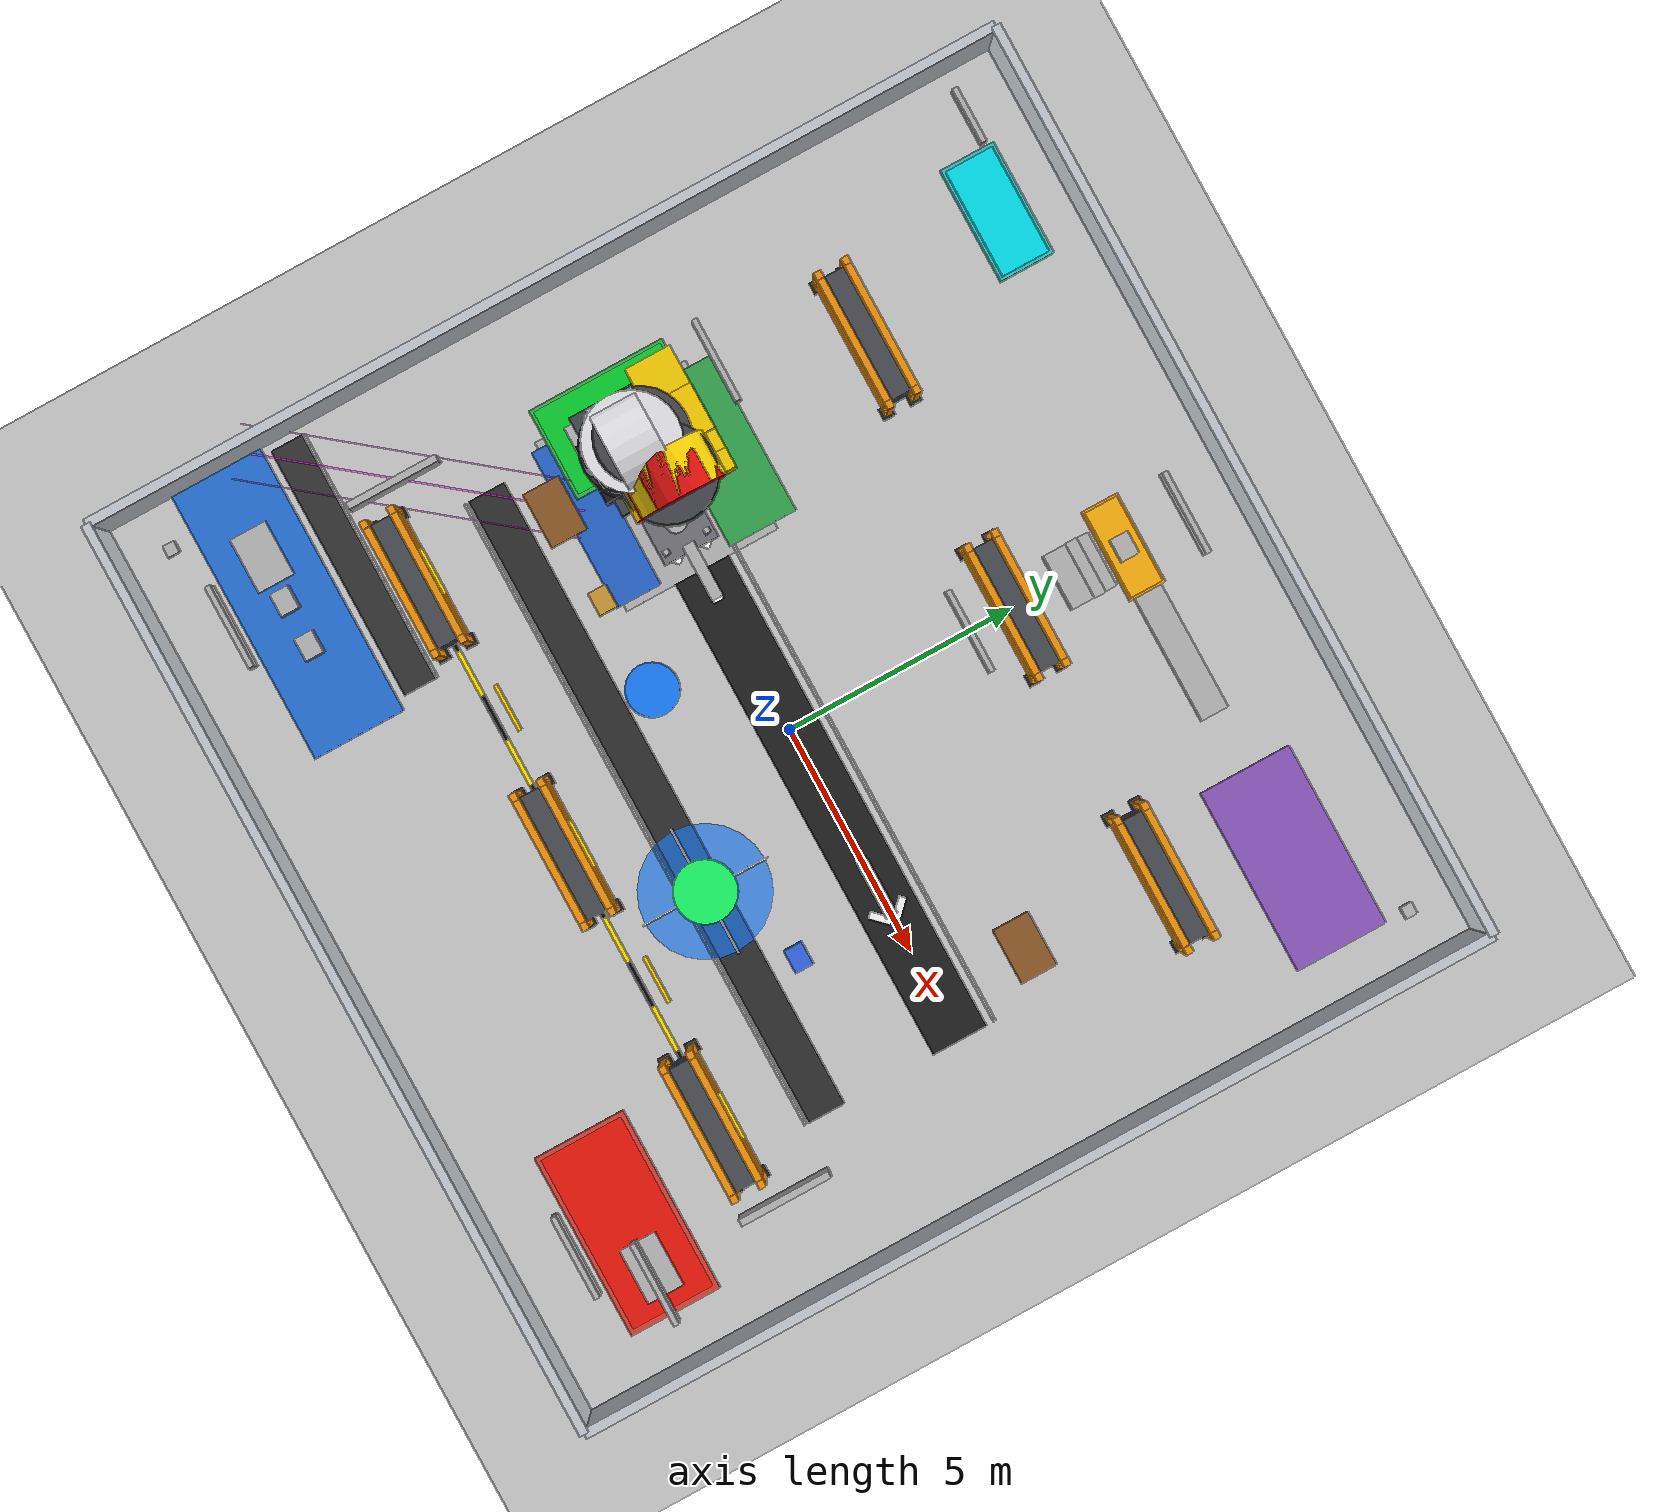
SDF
<?xml version="1.0"?>
<sdf version="1.7">
  <world name="warehouse">

    <physics type="ode">
      <max_step_size>0.002</max_step_size>
      <real_time_update_rate>500</real_time_update_rate>
    </physics>

    <include>
      <uri>model://sun</uri>
    </include>

    <include>
      <uri>model://ground_plane</uri>
    </include>

    <!-- Industrial Warehouse Scene -->
    <scene>
      <ambient>0.30 0.30 0.30 1</ambient>
      <background>0.12 0.15 0.18 1</background>
      <shadows>true</shadows>
      <grid>false</grid>
    </scene>

    <!-- Left Wall -->
    <model name="wall_left">
      <static>true</static>

      <link name="link">

        <collision name="collision">
          <geometry>
            <box>
              <size>20 0.2 2.5</size>
            </box>
          </geometry>
        </collision>

        <visual name="visual">
          <geometry>
            <box>
              <size>20 0.2 2.5</size>
            </box>
          </geometry>
          <material>
            <ambient>0.72 0.75 0.78 1</ambient>
            <diffuse>0.78 0.81 0.84 1</diffuse>
          </material>
        </visual>

        <pose>
          0 -10 1.25 0 0 0
        </pose>

      </link>

    </model>

    <!-- Right Wall -->
    <model name="wall_right">
      <static>true</static>

      <link name="link">

        <collision name="collision">
          <geometry>
            <box>
              <size>20 0.2 2.5</size>
            </box>
          </geometry>
        </collision>

        <visual name="visual">
          <geometry>
            <box>
              <size>20 0.2 2.5</size>
            </box>
          </geometry>
          <material>
            <ambient>0.72 0.75 0.78 1</ambient>
            <diffuse>0.78 0.81 0.84 1</diffuse>
          </material>
        </visual>

        <pose>
          0 10 1.25 0 0 0
        </pose>

      </link>

    </model>

    <!-- Front Wall -->
    <model name="wall_front">
      <static>true</static>

      <link name="link">

        <collision name="collision">
          <geometry>
            <box>
              <size>0.2 20 2.5</size>
            </box>
          </geometry>
        </collision>

        <visual name="visual">
          <geometry>
            <box>
              <size>0.2 20 2.5</size>
            </box>
          </geometry>
          <material>
            <ambient>0.72 0.75 0.78 1</ambient>
            <diffuse>0.78 0.81 0.84 1</diffuse>
          </material>
        </visual>

        <pose>
          10 0 1.25 0 0 0
        </pose>

      </link>

    </model>

    <!-- Back Wall -->
    <model name="wall_back">
      <static>true</static>

      <link name="link">

        <collision name="collision">
          <geometry>
            <box>
              <size>0.2 20 2.5</size>
            </box>
          </geometry>
        </collision>

        <visual name="visual">
          <geometry>
            <box>
              <size>0.2 20 2.5</size>
            </box>
          </geometry>
          <material>
            <ambient>0.72 0.75 0.78 1</ambient>
            <diffuse>0.78 0.81 0.84 1</diffuse>
          </material>
        </visual>

        <pose>
          -10 0 1.25 0 0 0
        </pose>

      </link>

    </model>

    <gui fullscreen="0">
      <camera name="user_camera">
        <pose>10 -10 8 0 0.5 2.3</pose>
      </camera>
    </gui>

    <!-- WAREHOUSE AISLES / FLOOR MARKINGS -->

    <!-- Main aisle -->
    <model name="aisle_main">
      <static>true</static>
      <pose>0 0 0.012 0 0 0</pose>
      <link name="link">
        <visual name="visual">
          <geometry>
            <box><size>14.0 1.2 0.02</size></box>
          </geometry>
          <material>
            <ambient>0.12 0.12 0.12 1</ambient>
            <diffuse>0.12 0.12 0.12 1</diffuse>
          </material>
        </visual>
      </link>
    </model>

    <!-- Cross aisle -->
    <model name="aisle_cross">
      <static>true</static>
      <pose>0 -3.0 0.013 0 0 0</pose>
      <link name="link">
        <visual name="visual">
          <geometry>
            <box><size>14.0 0.8 0.02</size></box>
          </geometry>
          <material>
            <ambient>0.18 0.18 0.18 1</ambient>
            <diffuse>0.18 0.18 0.18 1</diffuse>
          </material>
        </visual>
      </link>
    </model>

    <!-- Receiving aisle -->
    <model name="aisle_receiving">
      <static>true</static>
      <pose>-7.0 -6.0 0.014 0 0 0</pose>
      <link name="link">
        <visual name="visual">
          <geometry>
            <box><size>5.5 0.7 0.02</size></box>
          </geometry>
          <material>
            <ambient>0.20 0.20 0.20 1</ambient>
            <diffuse>0.20 0.20 0.20 1</diffuse>
          </material>
        </visual>
      </link>
    </model>

    <!-- Shelf 1  (-6, -5) -->
    <!-- Warehouse Rack 1 -->
    <model name="shelf_1">
      <static>true</static>
      <pose>-6 -5 0 0 0 0</pose>

      <!-- Conservative collision volume retained for Nav2 compatibility -->
      <link name="collision_frame">
        <collision name="collision">
          <geometry>
            <box>
              <size>3.0 0.8 2.4</size>
            </box>
          </geometry>
        </collision>
      </link>

      <!-- INDUSTRIAL PALLET RACK VISUAL FRAME -->

      <!-- Front uprights -->
      <link name="upright_front_left">
        <visual name="visual">
          <geometry>
            <box><size>0.16 0.16 2.4</size></box>
          </geometry>
          <pose>-1.42 -0.30 1.20 0 0 0</pose>
          <material>
            <ambient>0.80 0.45 0.04 1</ambient>
            <diffuse>0.95 0.58 0.05 1</diffuse>
          </material>
        </visual>
      </link>

      <link name="upright_front_right">
        <visual name="visual">
          <geometry>
            <box><size>0.16 0.16 2.4</size></box>
          </geometry>
          <pose>1.42 -0.30 1.20 0 0 0</pose>
          <material>
            <ambient>0.80 0.45 0.04 1</ambient>
            <diffuse>0.95 0.58 0.05 1</diffuse>
          </material>
        </visual>
      </link>

      <!-- Rear uprights -->
      <link name="upright_rear_left">
        <visual name="visual">
          <geometry>
            <box><size>0.16 0.16 2.4</size></box>
          </geometry>
          <pose>-1.42 0.30 1.20 0 0 0</pose>
          <material>
            <ambient>0.80 0.45 0.04 1</ambient>
            <diffuse>0.95 0.58 0.05 1</diffuse>
          </material>
        </visual>
      </link>

      <link name="upright_rear_right">
        <visual name="visual">
          <geometry>
            <box><size>0.16 0.16 2.4</size></box>
          </geometry>
          <pose>1.42 0.30 1.20 0 0 0</pose>
          <material>
            <ambient>0.80 0.45 0.04 1</ambient>
            <diffuse>0.95 0.58 0.05 1</diffuse>
          </material>
        </visual>
      </link>

      <!-- Top beams -->
      <link name="top_beam_front">
        <visual name="visual">
          <geometry>
            <box><size>2.90 0.16 0.16</size></box>
          </geometry>
          <pose>0 -0.30 2.28 0 0 0</pose>
          <material>
            <ambient>0.80 0.45 0.04 1</ambient>
            <diffuse>0.95 0.58 0.05 1</diffuse>
          </material>
        </visual>
      </link>

      <link name="top_beam_rear">
        <visual name="visual">
          <geometry>
            <box><size>2.90 0.16 0.16</size></box>
          </geometry>
          <pose>0 0.30 2.28 0 0 0</pose>
          <material>
            <ambient>0.80 0.45 0.04 1</ambient>
            <diffuse>0.95 0.58 0.05 1</diffuse>
          </material>
        </visual>
      </link>

      <!-- Storage level beams -->
      <link name="level_1_front">
        <visual name="visual">
          <geometry>
            <box><size>2.90 0.16 0.16</size></box>
          </geometry>
          <pose>0 -0.30 0.55 0 0 0</pose>
          <material>
            <ambient>0.80 0.45 0.04 1</ambient>
            <diffuse>0.95 0.58 0.05 1</diffuse>
          </material>
        </visual>
      </link>

      <link name="level_1_rear">
        <visual name="visual">
          <geometry>
            <box><size>2.90 0.16 0.16</size></box>
          </geometry>
          <pose>0 0.30 0.55 0 0 0</pose>
          <material>
            <ambient>0.80 0.45 0.04 1</ambient>
            <diffuse>0.95 0.58 0.05 1</diffuse>
          </material>
        </visual>
      </link>

      <link name="level_2_front">
        <visual name="visual">
          <geometry>
            <box><size>2.90 0.16 0.16</size></box>
          </geometry>
          <pose>0 -0.30 1.35 0 0 0</pose>
          <material>
            <ambient>0.80 0.45 0.04 1</ambient>
            <diffuse>0.95 0.58 0.05 1</diffuse>
          </material>
        </visual>
      </link>

      <link name="level_2_rear">
        <visual name="visual">
          <geometry>
            <box><size>2.90 0.16 0.16</size></box>
          </geometry>
          <pose>0 0.30 1.35 0 0 0</pose>
          <material>
            <ambient>0.80 0.45 0.04 1</ambient>
            <diffuse>0.95 0.58 0.05 1</diffuse>
          </material>
        </visual>
      </link>

      <link name="level_3_front">
        <visual name="visual">
          <geometry>
            <box><size>2.90 0.16 0.16</size></box>
          </geometry>
          <pose>0 -0.30 2.10 0 0 0</pose>
          <material>
            <ambient>0.80 0.45 0.04 1</ambient>
            <diffuse>0.95 0.58 0.05 1</diffuse>
          </material>
        </visual>
      </link>

      <link name="level_3_rear">
        <visual name="visual">
          <geometry>
            <box><size>2.90 0.16 0.16</size></box>
          </geometry>
          <pose>0 0.30 2.10 0 0 0</pose>
          <material>
            <ambient>0.80 0.45 0.04 1</ambient>
            <diffuse>0.95 0.58 0.05 1</diffuse>
          </material>
        </visual>
      </link>

      <!-- Shelf decks -->
      <link name="deck_1">
        <visual name="visual">
          <geometry>
            <box><size>2.72 0.56 0.10</size></box>
          </geometry>
          <pose>0 0 0.49 0 0 0</pose>
          <material>
            <ambient>0.18 0.20 0.22 1</ambient>
            <diffuse>0.28 0.30 0.32 1</diffuse>
          </material>
        </visual>
      </link>

      <link name="deck_2">
        <visual name="visual">
          <geometry>
            <box><size>2.72 0.56 0.10</size></box>
          </geometry>
          <pose>0 0 1.29 0 0 0</pose>
          <material>
            <ambient>0.18 0.20 0.22 1</ambient>
            <diffuse>0.28 0.30 0.32 1</diffuse>
          </material>
        </visual>
      </link>

      <link name="deck_3">
        <visual name="visual">
          <geometry>
            <box><size>2.72 0.56 0.10</size></box>
          </geometry>
          <pose>0 0 2.04 0 0 0</pose>
          <material>
            <ambient>0.18 0.20 0.22 1</ambient>
            <diffuse>0.28 0.30 0.32 1</diffuse>
          </material>
        </visual>
      </link>

      <!-- Base plates -->
      <link name="base_plate_left_front">
        <visual name="visual">
          <geometry>
            <box><size>0.26 0.26 0.07</size></box>
          </geometry>
          <pose>-1.42 -0.30 0.025 0 0 0</pose>
          <material>
            <ambient>0.20 0.20 0.20 1</ambient>
            <diffuse>0.25 0.25 0.25 1</diffuse>
          </material>
        </visual>
      </link>

      <link name="base_plate_right_front">
        <visual name="visual">
          <geometry>
            <box><size>0.26 0.26 0.07</size></box>
          </geometry>
          <pose>1.42 -0.30 0.025 0 0 0</pose>
          <material>
            <ambient>0.20 0.20 0.20 1</ambient>
            <diffuse>0.25 0.25 0.25 1</diffuse>
          </material>
        </visual>
      </link>

      <link name="base_plate_left_rear">
        <visual name="visual">
          <geometry>
            <box><size>0.26 0.26 0.07</size></box>
          </geometry>
          <pose>-1.42 0.30 0.025 0 0 0</pose>
          <material>
            <ambient>0.20 0.20 0.20 1</ambient>
            <diffuse>0.25 0.25 0.25 1</diffuse>
          </material>
        </visual>
      </link>

      <link name="base_plate_right_rear">
        <visual name="visual">
          <geometry>
            <box><size>0.26 0.26 0.07</size></box>
          </geometry>
          <pose>1.42 0.30 0.025 0 0 0</pose>
          <material>
            <ambient>0.20 0.20 0.20 1</ambient>
            <diffuse>0.25 0.25 0.25 1</diffuse>
          </material>
        </visual>
      </link>

    </model>

    <!-- Shelf 2  (0, -5) -->
    <!-- Warehouse Rack 2 -->
    <model name="shelf_2">
      <static>true</static>
      <pose>0 -5 0 0 0 0</pose>

      <!-- Conservative collision volume retained for Nav2 compatibility -->
      <link name="collision_frame">
        <collision name="collision">
          <geometry>
            <box>
              <size>3.0 0.8 2.4</size>
            </box>
          </geometry>
        </collision>
      </link>

      <!-- INDUSTRIAL PALLET RACK VISUAL FRAME -->

      <!-- Front uprights -->
      <link name="upright_front_left">
        <visual name="visual">
          <geometry>
            <box><size>0.16 0.16 2.4</size></box>
          </geometry>
          <pose>-1.42 -0.30 1.20 0 0 0</pose>
          <material>
            <ambient>0.80 0.45 0.04 1</ambient>
            <diffuse>0.95 0.58 0.05 1</diffuse>
          </material>
        </visual>
      </link>

      <link name="upright_front_right">
        <visual name="visual">
          <geometry>
            <box><size>0.16 0.16 2.4</size></box>
          </geometry>
          <pose>1.42 -0.30 1.20 0 0 0</pose>
          <material>
            <ambient>0.80 0.45 0.04 1</ambient>
            <diffuse>0.95 0.58 0.05 1</diffuse>
          </material>
        </visual>
      </link>

      <!-- Rear uprights -->
      <link name="upright_rear_left">
        <visual name="visual">
          <geometry>
            <box><size>0.16 0.16 2.4</size></box>
          </geometry>
          <pose>-1.42 0.30 1.20 0 0 0</pose>
          <material>
            <ambient>0.80 0.45 0.04 1</ambient>
            <diffuse>0.95 0.58 0.05 1</diffuse>
          </material>
        </visual>
      </link>

      <link name="upright_rear_right">
        <visual name="visual">
          <geometry>
            <box><size>0.16 0.16 2.4</size></box>
          </geometry>
          <pose>1.42 0.30 1.20 0 0 0</pose>
          <material>
            <ambient>0.80 0.45 0.04 1</ambient>
            <diffuse>0.95 0.58 0.05 1</diffuse>
          </material>
        </visual>
      </link>

      <!-- Top beams -->
      <link name="top_beam_front">
        <visual name="visual">
          <geometry>
            <box><size>2.90 0.16 0.16</size></box>
          </geometry>
          <pose>0 -0.30 2.28 0 0 0</pose>
          <material>
            <ambient>0.80 0.45 0.04 1</ambient>
            <diffuse>0.95 0.58 0.05 1</diffuse>
          </material>
        </visual>
      </link>

      <link name="top_beam_rear">
        <visual name="visual">
          <geometry>
            <box><size>2.90 0.16 0.16</size></box>
          </geometry>
          <pose>0 0.30 2.28 0 0 0</pose>
          <material>
            <ambient>0.80 0.45 0.04 1</ambient>
            <diffuse>0.95 0.58 0.05 1</diffuse>
          </material>
        </visual>
      </link>

      <!-- Storage level beams -->
      <link name="level_1_front">
        <visual name="visual">
          <geometry>
            <box><size>2.90 0.16 0.16</size></box>
          </geometry>
          <pose>0 -0.30 0.55 0 0 0</pose>
          <material>
            <ambient>0.80 0.45 0.04 1</ambient>
            <diffuse>0.95 0.58 0.05 1</diffuse>
          </material>
        </visual>
      </link>

      <link name="level_1_rear">
        <visual name="visual">
          <geometry>
            <box><size>2.90 0.16 0.16</size></box>
          </geometry>
          <pose>0 0.30 0.55 0 0 0</pose>
          <material>
            <ambient>0.80 0.45 0.04 1</ambient>
            <diffuse>0.95 0.58 0.05 1</diffuse>
          </material>
        </visual>
      </link>

      <link name="level_2_front">
        <visual name="visual">
          <geometry>
            <box><size>2.90 0.16 0.16</size></box>
          </geometry>
          <pose>0 -0.30 1.35 0 0 0</pose>
          <material>
            <ambient>0.80 0.45 0.04 1</ambient>
            <diffuse>0.95 0.58 0.05 1</diffuse>
          </material>
        </visual>
      </link>

      <link name="level_2_rear">
        <visual name="visual">
          <geometry>
            <box><size>2.90 0.16 0.16</size></box>
          </geometry>
          <pose>0 0.30 1.35 0 0 0</pose>
          <material>
            <ambient>0.80 0.45 0.04 1</ambient>
            <diffuse>0.95 0.58 0.05 1</diffuse>
          </material>
        </visual>
      </link>

      <link name="level_3_front">
        <visual name="visual">
          <geometry>
            <box><size>2.90 0.16 0.16</size></box>
          </geometry>
          <pose>0 -0.30 2.10 0 0 0</pose>
          <material>
            <ambient>0.80 0.45 0.04 1</ambient>
            <diffuse>0.95 0.58 0.05 1</diffuse>
          </material>
        </visual>
      </link>

      <link name="level_3_rear">
        <visual name="visual">
          <geometry>
            <box><size>2.90 0.16 0.16</size></box>
          </geometry>
          <pose>0 0.30 2.10 0 0 0</pose>
          <material>
            <ambient>0.80 0.45 0.04 1</ambient>
            <diffuse>0.95 0.58 0.05 1</diffuse>
          </material>
        </visual>
      </link>

      <!-- Shelf decks -->
      <link name="deck_1">
        <visual name="visual">
          <geometry>
            <box><size>2.72 0.56 0.10</size></box>
          </geometry>
          <pose>0 0 0.49 0 0 0</pose>
          <material>
            <ambient>0.18 0.20 0.22 1</ambient>
            <diffuse>0.28 0.30 0.32 1</diffuse>
          </material>
        </visual>
      </link>

      <link name="deck_2">
        <visual name="visual">
          <geometry>
            <box><size>2.72 0.56 0.10</size></box>
          </geometry>
          <pose>0 0 1.29 0 0 0</pose>
          <material>
            <ambient>0.18 0.20 0.22 1</ambient>
            <diffuse>0.28 0.30 0.32 1</diffuse>
          </material>
        </visual>
      </link>

      <link name="deck_3">
        <visual name="visual">
          <geometry>
            <box><size>2.72 0.56 0.10</size></box>
          </geometry>
          <pose>0 0 2.04 0 0 0</pose>
          <material>
            <ambient>0.18 0.20 0.22 1</ambient>
            <diffuse>0.28 0.30 0.32 1</diffuse>
          </material>
        </visual>
      </link>

      <!-- Base plates -->
      <link name="base_plate_left_front">
        <visual name="visual">
          <geometry>
            <box><size>0.26 0.26 0.07</size></box>
          </geometry>
          <pose>-1.42 -0.30 0.025 0 0 0</pose>
          <material>
            <ambient>0.20 0.20 0.20 1</ambient>
            <diffuse>0.25 0.25 0.25 1</diffuse>
          </material>
        </visual>
      </link>

      <link name="base_plate_right_front">
        <visual name="visual">
          <geometry>
            <box><size>0.26 0.26 0.07</size></box>
          </geometry>
          <pose>1.42 -0.30 0.025 0 0 0</pose>
          <material>
            <ambient>0.20 0.20 0.20 1</ambient>
            <diffuse>0.25 0.25 0.25 1</diffuse>
          </material>
        </visual>
      </link>

      <link name="base_plate_left_rear">
        <visual name="visual">
          <geometry>
            <box><size>0.26 0.26 0.07</size></box>
          </geometry>
          <pose>-1.42 0.30 0.025 0 0 0</pose>
          <material>
            <ambient>0.20 0.20 0.20 1</ambient>
            <diffuse>0.25 0.25 0.25 1</diffuse>
          </material>
        </visual>
      </link>

      <link name="base_plate_right_rear">
        <visual name="visual">
          <geometry>
            <box><size>0.26 0.26 0.07</size></box>
          </geometry>
          <pose>1.42 0.30 0.025 0 0 0</pose>
          <material>
            <ambient>0.20 0.20 0.20 1</ambient>
            <diffuse>0.25 0.25 0.25 1</diffuse>
          </material>
        </visual>
      </link>

    </model>

    <!-- Shelf 3  (6, -5) -->
    <!-- Warehouse Rack 3 -->
    <model name="shelf_3">
      <static>true</static>
      <pose>6 -5 0 0 0 0</pose>

      <!-- Conservative collision volume retained for Nav2 compatibility -->
      <link name="collision_frame">
        <collision name="collision">
          <geometry>
            <box>
              <size>3.0 0.8 2.4</size>
            </box>
          </geometry>
        </collision>
      </link>

      <!-- INDUSTRIAL PALLET RACK VISUAL FRAME -->

      <!-- Front uprights -->
      <link name="upright_front_left">
        <visual name="visual">
          <geometry>
            <box><size>0.16 0.16 2.4</size></box>
          </geometry>
          <pose>-1.42 -0.30 1.20 0 0 0</pose>
          <material>
            <ambient>0.80 0.45 0.04 1</ambient>
            <diffuse>0.95 0.58 0.05 1</diffuse>
          </material>
        </visual>
      </link>

      <link name="upright_front_right">
        <visual name="visual">
          <geometry>
            <box><size>0.16 0.16 2.4</size></box>
          </geometry>
          <pose>1.42 -0.30 1.20 0 0 0</pose>
          <material>
            <ambient>0.80 0.45 0.04 1</ambient>
            <diffuse>0.95 0.58 0.05 1</diffuse>
          </material>
        </visual>
      </link>

      <!-- Rear uprights -->
      <link name="upright_rear_left">
        <visual name="visual">
          <geometry>
            <box><size>0.16 0.16 2.4</size></box>
          </geometry>
          <pose>-1.42 0.30 1.20 0 0 0</pose>
          <material>
            <ambient>0.80 0.45 0.04 1</ambient>
            <diffuse>0.95 0.58 0.05 1</diffuse>
          </material>
        </visual>
      </link>

      <link name="upright_rear_right">
        <visual name="visual">
          <geometry>
            <box><size>0.16 0.16 2.4</size></box>
          </geometry>
          <pose>1.42 0.30 1.20 0 0 0</pose>
          <material>
            <ambient>0.80 0.45 0.04 1</ambient>
            <diffuse>0.95 0.58 0.05 1</diffuse>
          </material>
        </visual>
      </link>

      <!-- Top beams -->
      <link name="top_beam_front">
        <visual name="visual">
          <geometry>
            <box><size>2.90 0.16 0.16</size></box>
          </geometry>
          <pose>0 -0.30 2.28 0 0 0</pose>
          <material>
            <ambient>0.80 0.45 0.04 1</ambient>
            <diffuse>0.95 0.58 0.05 1</diffuse>
          </material>
        </visual>
      </link>

      <link name="top_beam_rear">
        <visual name="visual">
          <geometry>
            <box><size>2.90 0.16 0.16</size></box>
          </geometry>
          <pose>0 0.30 2.28 0 0 0</pose>
          <material>
            <ambient>0.80 0.45 0.04 1</ambient>
            <diffuse>0.95 0.58 0.05 1</diffuse>
          </material>
        </visual>
      </link>

      <!-- Storage level beams -->
      <link name="level_1_front">
        <visual name="visual">
          <geometry>
            <box><size>2.90 0.16 0.16</size></box>
          </geometry>
          <pose>0 -0.30 0.55 0 0 0</pose>
          <material>
            <ambient>0.80 0.45 0.04 1</ambient>
            <diffuse>0.95 0.58 0.05 1</diffuse>
          </material>
        </visual>
      </link>

      <link name="level_1_rear">
        <visual name="visual">
          <geometry>
            <box><size>2.90 0.16 0.16</size></box>
          </geometry>
          <pose>0 0.30 0.55 0 0 0</pose>
          <material>
            <ambient>0.80 0.45 0.04 1</ambient>
            <diffuse>0.95 0.58 0.05 1</diffuse>
          </material>
        </visual>
      </link>

      <link name="level_2_front">
        <visual name="visual">
          <geometry>
            <box><size>2.90 0.16 0.16</size></box>
          </geometry>
          <pose>0 -0.30 1.35 0 0 0</pose>
          <material>
            <ambient>0.80 0.45 0.04 1</ambient>
            <diffuse>0.95 0.58 0.05 1</diffuse>
          </material>
        </visual>
      </link>

      <link name="level_2_rear">
        <visual name="visual">
          <geometry>
            <box><size>2.90 0.16 0.16</size></box>
          </geometry>
          <pose>0 0.30 1.35 0 0 0</pose>
          <material>
            <ambient>0.80 0.45 0.04 1</ambient>
            <diffuse>0.95 0.58 0.05 1</diffuse>
          </material>
        </visual>
      </link>

      <link name="level_3_front">
        <visual name="visual">
          <geometry>
            <box><size>2.90 0.16 0.16</size></box>
          </geometry>
          <pose>0 -0.30 2.10 0 0 0</pose>
          <material>
            <ambient>0.80 0.45 0.04 1</ambient>
            <diffuse>0.95 0.58 0.05 1</diffuse>
          </material>
        </visual>
      </link>

      <link name="level_3_rear">
        <visual name="visual">
          <geometry>
            <box><size>2.90 0.16 0.16</size></box>
          </geometry>
          <pose>0 0.30 2.10 0 0 0</pose>
          <material>
            <ambient>0.80 0.45 0.04 1</ambient>
            <diffuse>0.95 0.58 0.05 1</diffuse>
          </material>
        </visual>
      </link>

      <!-- Shelf decks -->
      <link name="deck_1">
        <visual name="visual">
          <geometry>
            <box><size>2.72 0.56 0.10</size></box>
          </geometry>
          <pose>0 0 0.49 0 0 0</pose>
          <material>
            <ambient>0.18 0.20 0.22 1</ambient>
            <diffuse>0.28 0.30 0.32 1</diffuse>
          </material>
        </visual>
      </link>

      <link name="deck_2">
        <visual name="visual">
          <geometry>
            <box><size>2.72 0.56 0.10</size></box>
          </geometry>
          <pose>0 0 1.29 0 0 0</pose>
          <material>
            <ambient>0.18 0.20 0.22 1</ambient>
            <diffuse>0.28 0.30 0.32 1</diffuse>
          </material>
        </visual>
      </link>

      <link name="deck_3">
        <visual name="visual">
          <geometry>
            <box><size>2.72 0.56 0.10</size></box>
          </geometry>
          <pose>0 0 2.04 0 0 0</pose>
          <material>
            <ambient>0.18 0.20 0.22 1</ambient>
            <diffuse>0.28 0.30 0.32 1</diffuse>
          </material>
        </visual>
      </link>

      <!-- Base plates -->
      <link name="base_plate_left_front">
        <visual name="visual">
          <geometry>
            <box><size>0.26 0.26 0.07</size></box>
          </geometry>
          <pose>-1.42 -0.30 0.025 0 0 0</pose>
          <material>
            <ambient>0.20 0.20 0.20 1</ambient>
            <diffuse>0.25 0.25 0.25 1</diffuse>
          </material>
        </visual>
      </link>

      <link name="base_plate_right_front">
        <visual name="visual">
          <geometry>
            <box><size>0.26 0.26 0.07</size></box>
          </geometry>
          <pose>1.42 -0.30 0.025 0 0 0</pose>
          <material>
            <ambient>0.20 0.20 0.20 1</ambient>
            <diffuse>0.25 0.25 0.25 1</diffuse>
          </material>
        </visual>
      </link>

      <link name="base_plate_left_rear">
        <visual name="visual">
          <geometry>
            <box><size>0.26 0.26 0.07</size></box>
          </geometry>
          <pose>-1.42 0.30 0.025 0 0 0</pose>
          <material>
            <ambient>0.20 0.20 0.20 1</ambient>
            <diffuse>0.25 0.25 0.25 1</diffuse>
          </material>
        </visual>
      </link>

      <link name="base_plate_right_rear">
        <visual name="visual">
          <geometry>
            <box><size>0.26 0.26 0.07</size></box>
          </geometry>
          <pose>1.42 0.30 0.025 0 0 0</pose>
          <material>
            <ambient>0.20 0.20 0.20 1</ambient>
            <diffuse>0.25 0.25 0.25 1</diffuse>
          </material>
        </visual>
      </link>

    </model>

    <!-- Shelf 4  (-6, 5) -->
    <!-- Warehouse Rack 4 -->
    <model name="shelf_4">
      <static>true</static>
      <pose>-6 5 0 0 0 0</pose>

      <!-- Conservative collision volume retained for Nav2 compatibility -->
      <link name="collision_frame">
        <collision name="collision">
          <geometry>
            <box>
              <size>3.0 0.8 2.4</size>
            </box>
          </geometry>
        </collision>
      </link>

      <!-- INDUSTRIAL PALLET RACK VISUAL FRAME -->

      <!-- Front uprights -->
      <link name="upright_front_left">
        <visual name="visual">
          <geometry>
            <box><size>0.16 0.16 2.4</size></box>
          </geometry>
          <pose>-1.42 -0.30 1.20 0 0 0</pose>
          <material>
            <ambient>0.80 0.45 0.04 1</ambient>
            <diffuse>0.95 0.58 0.05 1</diffuse>
          </material>
        </visual>
      </link>

      <link name="upright_front_right">
        <visual name="visual">
          <geometry>
            <box><size>0.16 0.16 2.4</size></box>
          </geometry>
          <pose>1.42 -0.30 1.20 0 0 0</pose>
          <material>
            <ambient>0.80 0.45 0.04 1</ambient>
            <diffuse>0.95 0.58 0.05 1</diffuse>
          </material>
        </visual>
      </link>

      <!-- Rear uprights -->
      <link name="upright_rear_left">
        <visual name="visual">
          <geometry>
            <box><size>0.16 0.16 2.4</size></box>
          </geometry>
          <pose>-1.42 0.30 1.20 0 0 0</pose>
          <material>
            <ambient>0.80 0.45 0.04 1</ambient>
            <diffuse>0.95 0.58 0.05 1</diffuse>
          </material>
        </visual>
      </link>

      <link name="upright_rear_right">
        <visual name="visual">
          <geometry>
            <box><size>0.16 0.16 2.4</size></box>
          </geometry>
          <pose>1.42 0.30 1.20 0 0 0</pose>
          <material>
            <ambient>0.80 0.45 0.04 1</ambient>
            <diffuse>0.95 0.58 0.05 1</diffuse>
          </material>
        </visual>
      </link>

      <!-- Top beams -->
      <link name="top_beam_front">
        <visual name="visual">
          <geometry>
            <box><size>2.90 0.16 0.16</size></box>
          </geometry>
          <pose>0 -0.30 2.28 0 0 0</pose>
          <material>
            <ambient>0.80 0.45 0.04 1</ambient>
            <diffuse>0.95 0.58 0.05 1</diffuse>
          </material>
        </visual>
      </link>

      <link name="top_beam_rear">
        <visual name="visual">
          <geometry>
            <box><size>2.90 0.16 0.16</size></box>
          </geometry>
          <pose>0 0.30 2.28 0 0 0</pose>
          <material>
            <ambient>0.80 0.45 0.04 1</ambient>
            <diffuse>0.95 0.58 0.05 1</diffuse>
          </material>
        </visual>
      </link>

      <!-- Storage level beams -->
      <link name="level_1_front">
        <visual name="visual">
          <geometry>
            <box><size>2.90 0.16 0.16</size></box>
          </geometry>
          <pose>0 -0.30 0.55 0 0 0</pose>
          <material>
            <ambient>0.80 0.45 0.04 1</ambient>
            <diffuse>0.95 0.58 0.05 1</diffuse>
          </material>
        </visual>
      </link>

      <link name="level_1_rear">
        <visual name="visual">
          <geometry>
            <box><size>2.90 0.16 0.16</size></box>
          </geometry>
          <pose>0 0.30 0.55 0 0 0</pose>
          <material>
            <ambient>0.80 0.45 0.04 1</ambient>
            <diffuse>0.95 0.58 0.05 1</diffuse>
          </material>
        </visual>
      </link>

      <link name="level_2_front">
        <visual name="visual">
          <geometry>
            <box><size>2.90 0.16 0.16</size></box>
          </geometry>
          <pose>0 -0.30 1.35 0 0 0</pose>
          <material>
            <ambient>0.80 0.45 0.04 1</ambient>
            <diffuse>0.95 0.58 0.05 1</diffuse>
          </material>
        </visual>
      </link>

      <link name="level_2_rear">
        <visual name="visual">
          <geometry>
            <box><size>2.90 0.16 0.16</size></box>
          </geometry>
          <pose>0 0.30 1.35 0 0 0</pose>
          <material>
            <ambient>0.80 0.45 0.04 1</ambient>
            <diffuse>0.95 0.58 0.05 1</diffuse>
          </material>
        </visual>
      </link>

      <link name="level_3_front">
        <visual name="visual">
          <geometry>
            <box><size>2.90 0.16 0.16</size></box>
          </geometry>
          <pose>0 -0.30 2.10 0 0 0</pose>
          <material>
            <ambient>0.80 0.45 0.04 1</ambient>
            <diffuse>0.95 0.58 0.05 1</diffuse>
          </material>
        </visual>
      </link>

      <link name="level_3_rear">
        <visual name="visual">
          <geometry>
            <box><size>2.90 0.16 0.16</size></box>
          </geometry>
          <pose>0 0.30 2.10 0 0 0</pose>
          <material>
            <ambient>0.80 0.45 0.04 1</ambient>
            <diffuse>0.95 0.58 0.05 1</diffuse>
          </material>
        </visual>
      </link>

      <!-- Shelf decks -->
      <link name="deck_1">
        <visual name="visual">
          <geometry>
            <box><size>2.72 0.56 0.10</size></box>
          </geometry>
          <pose>0 0 0.49 0 0 0</pose>
          <material>
            <ambient>0.18 0.20 0.22 1</ambient>
            <diffuse>0.28 0.30 0.32 1</diffuse>
          </material>
        </visual>
      </link>

      <link name="deck_2">
        <visual name="visual">
          <geometry>
            <box><size>2.72 0.56 0.10</size></box>
          </geometry>
          <pose>0 0 1.29 0 0 0</pose>
          <material>
            <ambient>0.18 0.20 0.22 1</ambient>
            <diffuse>0.28 0.30 0.32 1</diffuse>
          </material>
        </visual>
      </link>

      <link name="deck_3">
        <visual name="visual">
          <geometry>
            <box><size>2.72 0.56 0.10</size></box>
          </geometry>
          <pose>0 0 2.04 0 0 0</pose>
          <material>
            <ambient>0.18 0.20 0.22 1</ambient>
            <diffuse>0.28 0.30 0.32 1</diffuse>
          </material>
        </visual>
      </link>

      <!-- Base plates -->
      <link name="base_plate_left_front">
        <visual name="visual">
          <geometry>
            <box><size>0.26 0.26 0.07</size></box>
          </geometry>
          <pose>-1.42 -0.30 0.025 0 0 0</pose>
          <material>
            <ambient>0.20 0.20 0.20 1</ambient>
            <diffuse>0.25 0.25 0.25 1</diffuse>
          </material>
        </visual>
      </link>

      <link name="base_plate_right_front">
        <visual name="visual">
          <geometry>
            <box><size>0.26 0.26 0.07</size></box>
          </geometry>
          <pose>1.42 -0.30 0.025 0 0 0</pose>
          <material>
            <ambient>0.20 0.20 0.20 1</ambient>
            <diffuse>0.25 0.25 0.25 1</diffuse>
          </material>
        </visual>
      </link>

      <link name="base_plate_left_rear">
        <visual name="visual">
          <geometry>
            <box><size>0.26 0.26 0.07</size></box>
          </geometry>
          <pose>-1.42 0.30 0.025 0 0 0</pose>
          <material>
            <ambient>0.20 0.20 0.20 1</ambient>
            <diffuse>0.25 0.25 0.25 1</diffuse>
          </material>
        </visual>
      </link>

      <link name="base_plate_right_rear">
        <visual name="visual">
          <geometry>
            <box><size>0.26 0.26 0.07</size></box>
          </geometry>
          <pose>1.42 0.30 0.025 0 0 0</pose>
          <material>
            <ambient>0.20 0.20 0.20 1</ambient>
            <diffuse>0.25 0.25 0.25 1</diffuse>
          </material>
        </visual>
      </link>

    </model>

    <!-- Shelf 5  (0, 5) -->
    <!-- Warehouse Rack 5 -->
    <model name="shelf_5">
      <static>true</static>
      <pose>0 5 0 0 0 0</pose>

      <!-- Conservative collision volume retained for Nav2 compatibility -->
      <link name="collision_frame">
        <collision name="collision">
          <geometry>
            <box>
              <size>3.0 0.8 2.4</size>
            </box>
          </geometry>
        </collision>
      </link>

      <!-- INDUSTRIAL PALLET RACK VISUAL FRAME -->

      <!-- Front uprights -->
      <link name="upright_front_left">
        <visual name="visual">
          <geometry>
            <box><size>0.16 0.16 2.4</size></box>
          </geometry>
          <pose>-1.42 -0.30 1.20 0 0 0</pose>
          <material>
            <ambient>0.80 0.45 0.04 1</ambient>
            <diffuse>0.95 0.58 0.05 1</diffuse>
          </material>
        </visual>
      </link>

      <link name="upright_front_right">
        <visual name="visual">
          <geometry>
            <box><size>0.16 0.16 2.4</size></box>
          </geometry>
          <pose>1.42 -0.30 1.20 0 0 0</pose>
          <material>
            <ambient>0.80 0.45 0.04 1</ambient>
            <diffuse>0.95 0.58 0.05 1</diffuse>
          </material>
        </visual>
      </link>

      <!-- Rear uprights -->
      <link name="upright_rear_left">
        <visual name="visual">
          <geometry>
            <box><size>0.16 0.16 2.4</size></box>
          </geometry>
          <pose>-1.42 0.30 1.20 0 0 0</pose>
          <material>
            <ambient>0.80 0.45 0.04 1</ambient>
            <diffuse>0.95 0.58 0.05 1</diffuse>
          </material>
        </visual>
      </link>

      <link name="upright_rear_right">
        <visual name="visual">
          <geometry>
            <box><size>0.16 0.16 2.4</size></box>
          </geometry>
          <pose>1.42 0.30 1.20 0 0 0</pose>
          <material>
            <ambient>0.80 0.45 0.04 1</ambient>
            <diffuse>0.95 0.58 0.05 1</diffuse>
          </material>
        </visual>
      </link>

      <!-- Top beams -->
      <link name="top_beam_front">
        <visual name="visual">
          <geometry>
            <box><size>2.90 0.16 0.16</size></box>
          </geometry>
          <pose>0 -0.30 2.28 0 0 0</pose>
          <material>
            <ambient>0.80 0.45 0.04 1</ambient>
            <diffuse>0.95 0.58 0.05 1</diffuse>
          </material>
        </visual>
      </link>

      <link name="top_beam_rear">
        <visual name="visual">
          <geometry>
            <box><size>2.90 0.16 0.16</size></box>
          </geometry>
          <pose>0 0.30 2.28 0 0 0</pose>
          <material>
            <ambient>0.80 0.45 0.04 1</ambient>
            <diffuse>0.95 0.58 0.05 1</diffuse>
          </material>
        </visual>
      </link>

      <!-- Storage level beams -->
      <link name="level_1_front">
        <visual name="visual">
          <geometry>
            <box><size>2.90 0.16 0.16</size></box>
          </geometry>
          <pose>0 -0.30 0.55 0 0 0</pose>
          <material>
            <ambient>0.80 0.45 0.04 1</ambient>
            <diffuse>0.95 0.58 0.05 1</diffuse>
          </material>
        </visual>
      </link>

      <link name="level_1_rear">
        <visual name="visual">
          <geometry>
            <box><size>2.90 0.16 0.16</size></box>
          </geometry>
          <pose>0 0.30 0.55 0 0 0</pose>
          <material>
            <ambient>0.80 0.45 0.04 1</ambient>
            <diffuse>0.95 0.58 0.05 1</diffuse>
          </material>
        </visual>
      </link>

      <link name="level_2_front">
        <visual name="visual">
          <geometry>
            <box><size>2.90 0.16 0.16</size></box>
          </geometry>
          <pose>0 -0.30 1.35 0 0 0</pose>
          <material>
            <ambient>0.80 0.45 0.04 1</ambient>
            <diffuse>0.95 0.58 0.05 1</diffuse>
          </material>
        </visual>
      </link>

      <link name="level_2_rear">
        <visual name="visual">
          <geometry>
            <box><size>2.90 0.16 0.16</size></box>
          </geometry>
          <pose>0 0.30 1.35 0 0 0</pose>
          <material>
            <ambient>0.80 0.45 0.04 1</ambient>
            <diffuse>0.95 0.58 0.05 1</diffuse>
          </material>
        </visual>
      </link>

      <link name="level_3_front">
        <visual name="visual">
          <geometry>
            <box><size>2.90 0.16 0.16</size></box>
          </geometry>
          <pose>0 -0.30 2.10 0 0 0</pose>
          <material>
            <ambient>0.80 0.45 0.04 1</ambient>
            <diffuse>0.95 0.58 0.05 1</diffuse>
          </material>
        </visual>
      </link>

      <link name="level_3_rear">
        <visual name="visual">
          <geometry>
            <box><size>2.90 0.16 0.16</size></box>
          </geometry>
          <pose>0 0.30 2.10 0 0 0</pose>
          <material>
            <ambient>0.80 0.45 0.04 1</ambient>
            <diffuse>0.95 0.58 0.05 1</diffuse>
          </material>
        </visual>
      </link>

      <!-- Shelf decks -->
      <link name="deck_1">
        <visual name="visual">
          <geometry>
            <box><size>2.72 0.56 0.10</size></box>
          </geometry>
          <pose>0 0 0.49 0 0 0</pose>
          <material>
            <ambient>0.18 0.20 0.22 1</ambient>
            <diffuse>0.28 0.30 0.32 1</diffuse>
          </material>
        </visual>
      </link>

      <link name="deck_2">
        <visual name="visual">
          <geometry>
            <box><size>2.72 0.56 0.10</size></box>
          </geometry>
          <pose>0 0 1.29 0 0 0</pose>
          <material>
            <ambient>0.18 0.20 0.22 1</ambient>
            <diffuse>0.28 0.30 0.32 1</diffuse>
          </material>
        </visual>
      </link>

      <link name="deck_3">
        <visual name="visual">
          <geometry>
            <box><size>2.72 0.56 0.10</size></box>
          </geometry>
          <pose>0 0 2.04 0 0 0</pose>
          <material>
            <ambient>0.18 0.20 0.22 1</ambient>
            <diffuse>0.28 0.30 0.32 1</diffuse>
          </material>
        </visual>
      </link>

      <!-- Base plates -->
      <link name="base_plate_left_front">
        <visual name="visual">
          <geometry>
            <box><size>0.26 0.26 0.07</size></box>
          </geometry>
          <pose>-1.42 -0.30 0.025 0 0 0</pose>
          <material>
            <ambient>0.20 0.20 0.20 1</ambient>
            <diffuse>0.25 0.25 0.25 1</diffuse>
          </material>
        </visual>
      </link>

      <link name="base_plate_right_front">
        <visual name="visual">
          <geometry>
            <box><size>0.26 0.26 0.07</size></box>
          </geometry>
          <pose>1.42 -0.30 0.025 0 0 0</pose>
          <material>
            <ambient>0.20 0.20 0.20 1</ambient>
            <diffuse>0.25 0.25 0.25 1</diffuse>
          </material>
        </visual>
      </link>

      <link name="base_plate_left_rear">
        <visual name="visual">
          <geometry>
            <box><size>0.26 0.26 0.07</size></box>
          </geometry>
          <pose>-1.42 0.30 0.025 0 0 0</pose>
          <material>
            <ambient>0.20 0.20 0.20 1</ambient>
            <diffuse>0.25 0.25 0.25 1</diffuse>
          </material>
        </visual>
      </link>

      <link name="base_plate_right_rear">
        <visual name="visual">
          <geometry>
            <box><size>0.26 0.26 0.07</size></box>
          </geometry>
          <pose>1.42 0.30 0.025 0 0 0</pose>
          <material>
            <ambient>0.20 0.20 0.20 1</ambient>
            <diffuse>0.25 0.25 0.25 1</diffuse>
          </material>
        </visual>
      </link>

    </model>

    <!-- Shelf 6  (6, 5) -->
    <!-- Warehouse Rack 6 -->
    <model name="shelf_6">
      <static>true</static>
      <pose>6 5 0 0 0 0</pose>

      <!-- Conservative collision volume retained for Nav2 compatibility -->
      <link name="collision_frame">
        <collision name="collision">
          <geometry>
            <box>
              <size>3.0 0.8 2.4</size>
            </box>
          </geometry>
        </collision>
      </link>

      <!-- INDUSTRIAL PALLET RACK VISUAL FRAME -->

      <!-- Front uprights -->
      <link name="upright_front_left">
        <visual name="visual">
          <geometry>
            <box><size>0.16 0.16 2.4</size></box>
          </geometry>
          <pose>-1.42 -0.30 1.20 0 0 0</pose>
          <material>
            <ambient>0.80 0.45 0.04 1</ambient>
            <diffuse>0.95 0.58 0.05 1</diffuse>
          </material>
        </visual>
      </link>

      <link name="upright_front_right">
        <visual name="visual">
          <geometry>
            <box><size>0.16 0.16 2.4</size></box>
          </geometry>
          <pose>1.42 -0.30 1.20 0 0 0</pose>
          <material>
            <ambient>0.80 0.45 0.04 1</ambient>
            <diffuse>0.95 0.58 0.05 1</diffuse>
          </material>
        </visual>
      </link>

      <!-- Rear uprights -->
      <link name="upright_rear_left">
        <visual name="visual">
          <geometry>
            <box><size>0.16 0.16 2.4</size></box>
          </geometry>
          <pose>-1.42 0.30 1.20 0 0 0</pose>
          <material>
            <ambient>0.80 0.45 0.04 1</ambient>
            <diffuse>0.95 0.58 0.05 1</diffuse>
          </material>
        </visual>
      </link>

      <link name="upright_rear_right">
        <visual name="visual">
          <geometry>
            <box><size>0.16 0.16 2.4</size></box>
          </geometry>
          <pose>1.42 0.30 1.20 0 0 0</pose>
          <material>
            <ambient>0.80 0.45 0.04 1</ambient>
            <diffuse>0.95 0.58 0.05 1</diffuse>
          </material>
        </visual>
      </link>

      <!-- Top beams -->
      <link name="top_beam_front">
        <visual name="visual">
          <geometry>
            <box><size>2.90 0.16 0.16</size></box>
          </geometry>
          <pose>0 -0.30 2.28 0 0 0</pose>
          <material>
            <ambient>0.80 0.45 0.04 1</ambient>
            <diffuse>0.95 0.58 0.05 1</diffuse>
          </material>
        </visual>
      </link>

      <link name="top_beam_rear">
        <visual name="visual">
          <geometry>
            <box><size>2.90 0.16 0.16</size></box>
          </geometry>
          <pose>0 0.30 2.28 0 0 0</pose>
          <material>
            <ambient>0.80 0.45 0.04 1</ambient>
            <diffuse>0.95 0.58 0.05 1</diffuse>
          </material>
        </visual>
      </link>

      <!-- Storage level beams -->
      <link name="level_1_front">
        <visual name="visual">
          <geometry>
            <box><size>2.90 0.16 0.16</size></box>
          </geometry>
          <pose>0 -0.30 0.55 0 0 0</pose>
          <material>
            <ambient>0.80 0.45 0.04 1</ambient>
            <diffuse>0.95 0.58 0.05 1</diffuse>
          </material>
        </visual>
      </link>

      <link name="level_1_rear">
        <visual name="visual">
          <geometry>
            <box><size>2.90 0.16 0.16</size></box>
          </geometry>
          <pose>0 0.30 0.55 0 0 0</pose>
          <material>
            <ambient>0.80 0.45 0.04 1</ambient>
            <diffuse>0.95 0.58 0.05 1</diffuse>
          </material>
        </visual>
      </link>

      <link name="level_2_front">
        <visual name="visual">
          <geometry>
            <box><size>2.90 0.16 0.16</size></box>
          </geometry>
          <pose>0 -0.30 1.35 0 0 0</pose>
          <material>
            <ambient>0.80 0.45 0.04 1</ambient>
            <diffuse>0.95 0.58 0.05 1</diffuse>
          </material>
        </visual>
      </link>

      <link name="level_2_rear">
        <visual name="visual">
          <geometry>
            <box><size>2.90 0.16 0.16</size></box>
          </geometry>
          <pose>0 0.30 1.35 0 0 0</pose>
          <material>
            <ambient>0.80 0.45 0.04 1</ambient>
            <diffuse>0.95 0.58 0.05 1</diffuse>
          </material>
        </visual>
      </link>

      <link name="level_3_front">
        <visual name="visual">
          <geometry>
            <box><size>2.90 0.16 0.16</size></box>
          </geometry>
          <pose>0 -0.30 2.10 0 0 0</pose>
          <material>
            <ambient>0.80 0.45 0.04 1</ambient>
            <diffuse>0.95 0.58 0.05 1</diffuse>
          </material>
        </visual>
      </link>

      <link name="level_3_rear">
        <visual name="visual">
          <geometry>
            <box><size>2.90 0.16 0.16</size></box>
          </geometry>
          <pose>0 0.30 2.10 0 0 0</pose>
          <material>
            <ambient>0.80 0.45 0.04 1</ambient>
            <diffuse>0.95 0.58 0.05 1</diffuse>
          </material>
        </visual>
      </link>

      <!-- Shelf decks -->
      <link name="deck_1">
        <visual name="visual">
          <geometry>
            <box><size>2.72 0.56 0.10</size></box>
          </geometry>
          <pose>0 0 0.49 0 0 0</pose>
          <material>
            <ambient>0.18 0.20 0.22 1</ambient>
            <diffuse>0.28 0.30 0.32 1</diffuse>
          </material>
        </visual>
      </link>

      <link name="deck_2">
        <visual name="visual">
          <geometry>
            <box><size>2.72 0.56 0.10</size></box>
          </geometry>
          <pose>0 0 1.29 0 0 0</pose>
          <material>
            <ambient>0.18 0.20 0.22 1</ambient>
            <diffuse>0.28 0.30 0.32 1</diffuse>
          </material>
        </visual>
      </link>

      <link name="deck_3">
        <visual name="visual">
          <geometry>
            <box><size>2.72 0.56 0.10</size></box>
          </geometry>
          <pose>0 0 2.04 0 0 0</pose>
          <material>
            <ambient>0.18 0.20 0.22 1</ambient>
            <diffuse>0.28 0.30 0.32 1</diffuse>
          </material>
        </visual>
      </link>

      <!-- Base plates -->
      <link name="base_plate_left_front">
        <visual name="visual">
          <geometry>
            <box><size>0.26 0.26 0.07</size></box>
          </geometry>
          <pose>-1.42 -0.30 0.025 0 0 0</pose>
          <material>
            <ambient>0.20 0.20 0.20 1</ambient>
            <diffuse>0.25 0.25 0.25 1</diffuse>
          </material>
        </visual>
      </link>

      <link name="base_plate_right_front">
        <visual name="visual">
          <geometry>
            <box><size>0.26 0.26 0.07</size></box>
          </geometry>
          <pose>1.42 -0.30 0.025 0 0 0</pose>
          <material>
            <ambient>0.20 0.20 0.20 1</ambient>
            <diffuse>0.25 0.25 0.25 1</diffuse>
          </material>
        </visual>
      </link>

      <link name="base_plate_left_rear">
        <visual name="visual">
          <geometry>
            <box><size>0.26 0.26 0.07</size></box>
          </geometry>
          <pose>-1.42 0.30 0.025 0 0 0</pose>
          <material>
            <ambient>0.20 0.20 0.20 1</ambient>
            <diffuse>0.25 0.25 0.25 1</diffuse>
          </material>
        </visual>
      </link>

      <link name="base_plate_right_rear">
        <visual name="visual">
          <geometry>
            <box><size>0.26 0.26 0.07</size></box>
          </geometry>
          <pose>1.42 0.30 0.025 0 0 0</pose>
          <material>
            <ambient>0.20 0.20 0.20 1</ambient>
            <diffuse>0.25 0.25 0.25 1</diffuse>
          </material>
        </visual>
      </link>

    </model>

    <!-- WAREHOUSE RACK CARGO -->

    <!-- Rack 1 cargo -->
    <model name="rack1_box_a">
      <static>true</static>
      <pose>-6.7 -5.0 0.82 0 0 0</pose>
      <link name="link">
        <visual name="visual">
          <geometry><box><size>0.55 0.55 0.50</size></box></geometry>
          <material>
            <ambient>0.65 0.42 0.18 1</ambient>
            <diffuse>0.65 0.42 0.18 1</diffuse>
          </material>
        </visual>
      </link>
    </model>

    <model name="rack1_box_b">
      <static>true</static>
      <pose>-6.0 -5.0 1.62 0 0 0</pose>
      <link name="link">
        <visual name="visual">
          <geometry><box><size>0.55 0.55 0.50</size></box></geometry>
          <material>
            <ambient>0.20 0.45 0.75 1</ambient>
            <diffuse>0.20 0.45 0.75 1</diffuse>
          </material>
        </visual>
      </link>
    </model>

    <!-- Rack 2 cargo -->
    <model name="rack2_box_a">
      <static>true</static>
      <pose>-0.7 -5.0 0.82 0 0 0</pose>
      <link name="link">
        <visual name="visual">
          <geometry><box><size>0.55 0.55 0.50</size></box></geometry>
          <material>
            <ambient>0.72 0.48 0.18 1</ambient>
            <diffuse>0.72 0.48 0.18 1</diffuse>
          </material>
        </visual>
      </link>
    </model>

    <model name="rack2_box_b">
      <static>true</static>
      <pose>0.0 -5.0 1.62 0 0 0</pose>
      <link name="link">
        <visual name="visual">
          <geometry><box><size>0.55 0.55 0.50</size></box></geometry>
          <material>
            <ambient>0.30 0.60 0.30 1</ambient>
            <diffuse>0.30 0.60 0.30 1</diffuse>
          </material>
        </visual>
      </link>
    </model>

    <!-- Rack 3 cargo -->
    <model name="rack3_box_a">
      <static>true</static>
      <pose>5.3 -5.0 0.82 0 0 0</pose>
      <link name="link">
        <visual name="visual">
          <geometry><box><size>0.55 0.55 0.50</size></box></geometry>
          <material>
            <ambient>0.72 0.30 0.20 1</ambient>
            <diffuse>0.72 0.30 0.20 1</diffuse>
          </material>
        </visual>
      </link>
    </model>

    <model name="rack3_box_b">
      <static>true</static>
      <pose>6.0 -5.0 1.62 0 0 0</pose>
      <link name="link">
        <visual name="visual">
          <geometry><box><size>0.55 0.55 0.50</size></box></geometry>
          <material>
            <ambient>0.25 0.50 0.75 1</ambient>
            <diffuse>0.25 0.50 0.75 1</diffuse>
          </material>
        </visual>
      </link>
    </model>

    <!-- Pallet -->

    <model name="pallet_1">
      <static>true</static>
      <pose>-6 -2 0.075 0 0 0</pose>
      <link name="link">
        <collision name="collision">
          <geometry>
            <box>
              <size>1.2 0.8 0.15</size>
            </box>
          </geometry>
        </collision>
        <visual name="visual">
          <geometry>
            <box>
              <size>1.2 0.8 0.15</size>
            </box>
          </geometry>
          <material>
            <ambient>0.55 0.35 0.15 1</ambient>
            <diffuse>0.55 0.35 0.15 1</diffuse>
          </material>
        </visual>
      </link>
    </model>

    <model name="pallet_2">
      <static>true</static>
      <pose>6 2 0.075 0 0 0</pose>
      <link name="link">
        <collision name="collision">
          <geometry>
            <box>
              <size>1.2 0.8 0.15</size>
            </box>
          </geometry>
        </collision>
        <visual name="visual">
          <geometry>
            <box>
              <size>1.2 0.8 0.15</size>
            </box>
          </geometry>
          <material>
            <ambient>0.55 0.35 0.15 1</ambient>
            <diffuse>0.55 0.35 0.15 1</diffuse>
          </material>
        </visual>
      </link>
    </model>

    <!-- Cargo Boxes -->

    <model name="box_1">
      <pose>-4 -2 0.55 0 0 0</pose>
      <static>true</static>
      <link name="link">
        <collision name="collision">
          <geometry>
            <box>
              <size>0.5 0.4 0.4</size>
            </box>
          </geometry>
        </collision>
        <visual name="visual">
          <geometry>
            <box>
              <size>0.5 0.4 0.4</size>
            </box>
          </geometry>
          <material>
            <ambient>0.8 0.6 0.2 1</ambient>
            <diffuse>0.8 0.6 0.2 1</diffuse>
          </material>
        </visual>
      </link>
    </model>

    <model name="box_2">
      <pose>4 -2 0.55 0 0 0</pose>
      <static>true</static>
      <link name="link">
        <collision name="collision">
          <geometry>
            <box>
              <size>0.5 0.4 0.4</size>
            </box>
          </geometry>
        </collision>
        <visual name="visual">
          <geometry>
            <box>
              <size>0.5 0.4 0.4</size>
            </box>
          </geometry>
          <material>
            <ambient>0.2 0.4 0.9 1</ambient>
            <diffuse>0.2 0.4 0.9 1</diffuse>
          </material>
        </visual>
      </link>
    </model>

    <!-- LOGISTICS WAREHOUSE ZONES -->

    <!-- Receiving / Inbound -->
    <model name="receiving_zone">
      <static>true</static>
      <pose>-7.0 -7.5 0.05 0 0 0</pose>
      <link name="link">
        <visual name="visual">

          <material>
            <ambient>0.10 0.30 0.65 1</ambient>
            <diffuse>0.15 0.45 0.85 1</diffuse>
          </material>
<geometry>
            <box><size>6.0 2.0 0.10</size></box>
          </geometry>
        </visual>
      </link>
    </model>

    <!-- Picking staging -->
    <model name="picking_zone">
      <static>true</static>
      <pose>-7.0 0 0.05 0 0 0</pose>
      <link name="link">
        <visual name="visual">

          <material>
            <ambient>0.12 0.45 0.18 1</ambient>
            <diffuse>0.20 0.70 0.30 1</diffuse>
          </material>
<geometry>
            <box><size>2.0 3.0 0.10</size></box>
          </geometry>
        </visual>
      </link>
    </model>

    <!-- Packing -->
    <model name="packing_zone">
      <static>true</static>
      <pose>0 7.5 0.18 0 0 0</pose>
      <link name="link">
        <visual name="visual">

          <material>
            <ambient>0.65 0.40 0.05 1</ambient>
            <diffuse>0.95 0.65 0.10 1</diffuse>
          </material>
<geometry>
            <box><size>2.0 0.8 0.25</size></box>
          </geometry>
        </visual>
      </link>
    </model>

    <!-- Delivery / Outbound -->
    <model name="delivery_zone">
      <static>true</static>
      <pose>7.0 -7.5 0.05 0 0 0</pose>
      <link name="link">
        <visual name="visual">

          <material>
            <ambient>0.55 0.12 0.10 1</ambient>
            <diffuse>0.85 0.25 0.20 1</diffuse>
          </material>
<geometry>
            <box><size>4.0 2.0 0.10</size></box>
          </geometry>
        </visual>
      </link>
    </model>

    <!-- Robot charging station -->
    <model name="charging_station">
      <static>true</static>
      <pose>-7.0 8.5 0.10 0 0 0</pose>
      <link name="link">
        <collision name="collision">
          <geometry>
            <box><size>2.5 1.2 0.20</size></box>
          </geometry>
        </collision>
        <visual name="visual">

          <material>
            <ambient>0.15 0.55 0.55 1</ambient>
            <diffuse>0.20 0.75 0.75 1</diffuse>
          </material>
<geometry>
            <box><size>2.5 1.2 0.20</size></box>
          </geometry>
        </visual>
      </link>
    </model>

    <!-- Robot staging / waiting -->
    <model name="robot_staging">
      <static>true</static>
      <pose>7.0 7.5 0.05 0 0 0</pose>
      <link name="link">
        <visual name="visual">

          <material>
            <ambient>0.32 0.18 0.48 1</ambient>
            <diffuse>0.55 0.35 0.75 1</diffuse>
          </material>
<geometry>
            <box><size>4.0 2.0 0.10</size></box>
          </geometry>
        </visual>
      </link>
    </model>

    <!-- W18 logistics objects -->
    <model name="pallet_3">
      <static>true</static>
      <pose>-8.0 -7.5 0.075 0 0 0</pose>
      <link name="link">
        <visual name="visual">
          <geometry><box><size>1.2 0.8 0.15</size></box></geometry>
        </visual>
      </link>
    </model>

    <model name="pallet_4">
      <static>true</static>
      <pose>8.0 -7.5 0.075 0 0 0</pose>
      <link name="link">
        <visual name="visual">
          <geometry><box><size>1.2 0.8 0.15</size></box></geometry>
        </visual>
      </link>
    </model>

    <model name="box_3">
      <static>true</static>
      <pose>-6.0 -7.5 0.35 0 0 0</pose>
      <link name="link">
        <visual name="visual">
          <geometry><box><size>0.5 0.4 0.4</size></box></geometry>
        </visual>
      </link>
    </model>

    <model name="box_4">
      <static>true</static>
      <pose>-7.0 -7.5 0.35 0 0 0</pose>
      <link name="link">
        <visual name="visual">
          <geometry><box><size>0.5 0.4 0.4</size></box></geometry>
        </visual>
      </link>
    </model>

    <model name="box_5">
      <static>true</static>
      <pose>-6.0 5.0 0.75 0 0 0</pose>
      <link name="link">
        <visual name="visual">
          <geometry><box><size>0.5 0.4 0.4</size></box></geometry>
        </visual>
      </link>
    </model>

    <model name="box_6">
      <static>true</static>
      <pose>0.0 5.0 1.55 0 0 0</pose>
      <link name="link">
        <visual name="visual">
          <geometry><box><size>0.5 0.4 0.4</size></box></geometry>
        </visual>
      </link>
    </model>

    <model name="box_7">
      <static>true</static>
      <pose>6.0 5.0 0.75 0 0 0</pose>
      <link name="link">
        <visual name="visual">
          <geometry><box><size>0.5 0.4 0.4</size></box></geometry>
        </visual>
      </link>
    </model>

    <model name="box_8">
      <static>true</static>
      <pose>0.0 7.5 0.35 0 0 0</pose>
      <link name="link">
        <visual name="visual">
          <geometry><box><size>0.5 0.4 0.4</size></box></geometry>
        </visual>
      </link>
    </model>

    <model name="tote_1">
      <static>true</static>
      <pose>-7.0 0.8 0.20 0 0 0</pose>
      <link name="link">
        <visual name="visual">
          <geometry><box><size>0.7 0.5 0.4</size></box></geometry>
        </visual>
      </link>
    </model>

    <model name="tote_2">
      <static>true</static>
      <pose>-7.0 -0.8 0.20 0 0 0</pose>
      <link name="link">
        <visual name="visual">
          <geometry><box><size>0.7 0.5 0.4</size></box></geometry>
        </visual>
      </link>
    </model>

    <model name="tote_3">
      <static>true</static>
      <pose>0.0 6.5 0.20 0 0 0</pose>
      <link name="link">
        <visual name="visual">
          <geometry><box><size>0.7 0.5 0.4</size></box></geometry>
        </visual>
      </link>
    </model>

    <!-- W19 Picking / Packing / Conveyor -->
    <model name="picking_station">
      <static>true</static>
      <pose>-5.5 0 0.30 0 0 0</pose>
      <link name="link">
        <visual name="visual">
          <geometry>
            <box><size>1.0 1.2 0.60</size></box>
          </geometry>
        </visual>
      </link>
    </model>

    <model name="packing_station">
      <static>true</static>
      <pose>0 6.5 0.30 0 0 0</pose>
      <link name="link">
        <visual name="visual">
          <geometry>
            <box><size>1.2 1.0 0.60</size></box>
          </geometry>
        </visual>
      </link>
    </model>

    <model name="conveyor_w19">
      <static>true</static>
      <pose>2.0 7.5 0.15 0 0 0</pose>
      <link name="link">
        <visual name="visual">
          <geometry>
            <box><size>3.5 0.6 0.30</size></box>
          </geometry>
        </visual>
      </link>
    </model>

    <!-- W21 COLLABORATIVE ROBOT WORKCELL -->

    <!-- Collaborative Workbench -->
    <model name="collab_workbench">
      <static>true</static>
      <pose>-5.5 0.0 0.65 0 0 0</pose>

      <link name="workbench">
        <collision name="collision">
          <geometry>
            <box>
              <size>3.0 1.2 0.15</size>
            </box>
          </geometry>
        </collision>

        <visual name="visual">
          <geometry>
            <box>
              <size>3.0 1.2 0.15</size>
            </box>
          </geometry>
          <material>
            <ambient>0.30 0.30 0.32 1</ambient>
            <diffuse>0.45 0.45 0.48 1</diffuse>
          </material>
        </visual>
      </link>

      <!-- Workbench legs -->
      <link name="leg_fl">
        <visual name="visual">
          <geometry>
            <box><size>0.12 0.12 0.65</size></box>
          </geometry>
          <pose>-1.30 -0.45 0.325 0 0 0</pose>
        </visual>
      </link>

      <link name="leg_fr">
        <visual name="visual">
          <geometry>
            <box><size>0.12 0.12 0.65</size></box>
          </geometry>
          <pose>1.30 -0.45 0.325 0 0 0</pose>
        </visual>
      </link>

      <link name="leg_rl">
        <visual name="visual">
          <geometry>
            <box><size>0.12 0.12 0.65</size></box>
          </geometry>
          <pose>-1.30 0.45 0.325 0 0 0</pose>
        </visual>
      </link>

      <link name="leg_rr">
        <visual name="visual">
          <geometry>
            <box><size>0.12 0.12 0.65</size></box>
          </geometry>
          <pose>1.30 0.45 0.325 0 0 0</pose>
        </visual>
      </link>
    </model>

    <!-- PANDA (FR3) WORKCELL — Visual-only, no collision     -->
    <!-- FR3 is MuJoCo-only at runtime. Gazebo = visual only. -->
    <!-- Position anchored to panda_workcell_mount at         -->
    <!-- (-6.35, 0.0, 0.73). Do NOT add ros2_control here.   -->

    <!-- Mounting cylinder — retained from original -->
    <model name="panda_workcell_mount">
      <static>true</static>
      <pose>-6.35 0.0 0.73 0 0 0</pose>
      <link name="link">
        <visual name="visual">
          <geometry>
            <cylinder>
              <radius>0.22</radius>
              <length>0.04</length>
            </cylinder>
          </geometry>
          <material>
            <ambient>0.08 0.09 0.10 1</ambient>
            <diffuse>0.12 0.13 0.14 1</diffuse>
          </material>
        </visual>
      </link>
    </model>

    <!-- ── Panda (FR3) Visual Robot Body ─────────────────── -->
    <!-- Base link — dark cylindrical housing                 -->
    <model name="panda_vis_base">
      <static>true</static>
      <pose>-6.35 0.0 0.80 0 0 0</pose>
      <link name="link">
        <visual name="base_body">
          <geometry><cylinder radius="0.076" length="0.130"/></geometry>
          <material>
            <ambient>0.88 0.88 0.90 1</ambient>
            <diffuse>0.92 0.92 0.94 1</diffuse>
          </material>
        </visual>
        <visual name="base_ring_top">
          <pose>0 0 0.068 0 0 0</pose>
          <geometry><cylinder radius="0.080" length="0.014"/></geometry>
          <material>
            <ambient>0.20 0.20 0.22 1</ambient>
            <diffuse>0.25 0.25 0.27 1</diffuse>
          </material>
        </visual>
        <visual name="base_bolt_0">
          <pose>0.068 0.0 -0.055 0 0 0</pose>
          <geometry><cylinder radius="0.007" length="0.016"/></geometry>
          <material><ambient>0.35 0.35 0.38 1</ambient><diffuse>0.40 0.40 0.43 1</diffuse></material>
        </visual>
        <visual name="base_bolt_1">
          <pose>-0.068 0.0 -0.055 0 0 0</pose>
          <geometry><cylinder radius="0.007" length="0.016"/></geometry>
          <material><ambient>0.35 0.35 0.38 1</ambient><diffuse>0.40 0.40 0.43 1</diffuse></material>
        </visual>
        <visual name="base_bolt_2">
          <pose>0.0 0.068 -0.055 0 0 0</pose>
          <geometry><cylinder radius="0.007" length="0.016"/></geometry>
          <material><ambient>0.35 0.35 0.38 1</ambient><diffuse>0.40 0.40 0.43 1</diffuse></material>
        </visual>
        <visual name="base_bolt_3">
          <pose>0.0 -0.068 -0.055 0 0 0</pose>
          <geometry><cylinder radius="0.007" length="0.016"/></geometry>
          <material><ambient>0.35 0.35 0.38 1</ambient><diffuse>0.40 0.40 0.43 1</diffuse></material>
        </visual>
      </link>
    </model>

    <!-- Link 1 — shoulder pan housing -->
    <model name="panda_vis_link1">
      <static>true</static>
      <pose>-6.35 0.0 0.946 0 0 0</pose>
      <link name="link">
        <visual name="l1_body">
          <geometry><cylinder radius="0.062" length="0.100"/></geometry>
          <material><ambient>0.88 0.88 0.90 1</ambient><diffuse>0.92 0.92 0.94 1</diffuse></material>
        </visual>
        <visual name="l1_ring">
          <pose>0 0 0.052 0 0 0</pose>
          <geometry><cylinder radius="0.066" length="0.012"/></geometry>
          <material><ambient>0.20 0.20 0.22 1</ambient><diffuse>0.25 0.25 0.27 1</diffuse></material>
        </visual>
      </link>
    </model>

    <!-- Link 2 — shoulder lift, articulated down -->
    <model name="panda_vis_link2">
      <static>true</static>
      <pose>-6.35 0.0 1.020 0.3 0 0</pose>
      <link name="link">
        <visual name="l2_cap">
          <geometry><cylinder radius="0.060" length="0.036"/></geometry>
          <material><ambient>0.20 0.20 0.22 1</ambient><diffuse>0.25 0.25 0.27 1</diffuse></material>
        </visual>
        <visual name="l2_tube">
          <pose>0 0.050 0.180 1.5708 0 0</pose>
          <geometry><cylinder radius="0.050" length="0.310"/></geometry>
          <material><ambient>0.88 0.88 0.90 1</ambient><diffuse>0.92 0.92 0.94 1</diffuse></material>
        </visual>
      </link>
    </model>

    <!-- Link 3+4 — elbow complex -->
    <model name="panda_vis_link34">
      <static>true</static>
      <pose>-6.35 0.0 1.360 -0.3 0 0</pose>
      <link name="link">
        <visual name="l3_cap">
          <geometry><cylinder radius="0.056" length="0.032"/></geometry>
          <material><ambient>0.20 0.20 0.22 1</ambient><diffuse>0.25 0.25 0.27 1</diffuse></material>
        </visual>
        <visual name="l3_tube">
          <pose>0 0.0 0.160 0 0 0</pose>
          <geometry><cylinder radius="0.044" length="0.280"/></geometry>
          <material><ambient>0.88 0.88 0.90 1</ambient><diffuse>0.92 0.92 0.94 1</diffuse></material>
        </visual>
        <visual name="l4_cap">
          <pose>0 0.0 0.296 0 0 0</pose>
          <geometry><cylinder radius="0.056" length="0.028"/></geometry>
          <material><ambient>0.20 0.20 0.22 1</ambient><diffuse>0.25 0.25 0.27 1</diffuse></material>
        </visual>
        <!-- Cable strip -->
        <visual name="l34_cable">
          <pose>0.046 0 0.160 0 0 0</pose>
          <geometry><box size="0.007 0.009 0.240"/></geometry>
          <material><ambient>0.08 0.08 0.10 1</ambient><diffuse>0.10 0.10 0.12 1</diffuse></material>
        </visual>
      </link>
    </model>

    <!-- Link 5+6+7 — wrist stack -->
    <model name="panda_vis_wrist">
      <static>true</static>
      <pose>-6.35 0.0 1.620 0.0 0 0</pose>
      <link name="link">
        <visual name="w1_body">
          <geometry><cylinder radius="0.042" length="0.088"/></geometry>
          <material><ambient>0.88 0.88 0.90 1</ambient><diffuse>0.92 0.92 0.94 1</diffuse></material>
        </visual>
        <visual name="w1_ring">
          <pose>0 0 0.046 0 0 0</pose>
          <geometry><cylinder radius="0.046" length="0.010"/></geometry>
          <material><ambient>0.20 0.20 0.22 1</ambient><diffuse>0.25 0.25 0.27 1</diffuse></material>
        </visual>
        <visual name="w2_body">
          <pose>0 0 0.118 1.5708 0 0</pose>
          <geometry><cylinder radius="0.040" length="0.078"/></geometry>
          <material><ambient>0.88 0.88 0.90 1</ambient><diffuse>0.92 0.92 0.94 1</diffuse></material>
        </visual>
        <visual name="w3_body">
          <pose>0 0 0.200 0 0 0</pose>
          <geometry><cylinder radius="0.034" length="0.058"/></geometry>
          <material><ambient>0.88 0.88 0.90 1</ambient><diffuse>0.92 0.92 0.94 1</diffuse></material>
        </visual>
      </link>
    </model>

    <!-- Franka Hand (end-effector) — visual only -->
    <model name="panda_vis_hand">
      <static>true</static>
      <pose>-6.35 0.0 1.700 0 0 0</pose>
      <link name="link">
        <!-- Hand body -->
        <visual name="hand_body">
          <geometry><box size="0.080 0.074 0.058"/></geometry>
          <material><ambient>0.20 0.20 0.22 1</ambient><diffuse>0.28 0.28 0.30 1</diffuse></material>
        </visual>
        <!-- Left finger -->
        <visual name="finger_l">
          <pose>-0.008 0 0.058 0 0 0</pose>
          <geometry><box size="0.012 0.018 0.060"/></geometry>
          <material><ambient>0.30 0.30 0.32 1</ambient><diffuse>0.35 0.35 0.38 1</diffuse></material>
        </visual>
        <!-- Right finger -->
        <visual name="finger_r">
          <pose>0.008 0 0.058 0 0 0</pose>
          <geometry><box size="0.012 0.018 0.060"/></geometry>
          <material><ambient>0.30 0.30 0.32 1</ambient><diffuse>0.35 0.35 0.38 1</diffuse></material>
        </visual>
        <!-- Flange disc -->
        <visual name="flange">
          <pose>0 0 -0.034 0 0 0</pose>
          <geometry><cylinder radius="0.040" length="0.010"/></geometry>
          <material><ambient>0.25 0.25 0.27 1</ambient><diffuse>0.30 0.30 0.33 1</diffuse></material>
        </visual>
      </link>
    </model>

    <!-- ── Panda Workcell Station Table ──────────────────── -->
    <model name="panda_station_table">
      <static>true</static>
      <pose>-6.35 0.0 0.365 0 0 0</pose>
      <link name="link">
        <!-- Tabletop brushed steel -->
        <visual name="tabletop">
          <pose>0 0 0.365 0 0 0</pose>
          <geometry><box size="1.30 0.85 0.032"/></geometry>
          <material>
            <ambient>0.68 0.70 0.72 1</ambient>
            <diffuse>0.72 0.74 0.76 1</diffuse>
          </material>
        </visual>
        <!-- Apron front -->
        <visual name="apron_f">
          <pose>0 -0.408 0.175 0 0 0</pose>
          <geometry><box size="1.26 0.024 0.360"/></geometry>
          <material><ambient>0.22 0.24 0.26 1</ambient><diffuse>0.26 0.28 0.30 1</diffuse></material>
        </visual>
        <!-- Apron back -->
        <visual name="apron_b">
          <pose>0 0.408 0.175 0 0 0</pose>
          <geometry><box size="1.26 0.024 0.360"/></geometry>
          <material><ambient>0.22 0.24 0.26 1</ambient><diffuse>0.26 0.28 0.30 1</diffuse></material>
        </visual>
        <!-- Leg FL -->
        <visual name="leg_fl">
          <pose>-0.600 -0.370 -0.150 0 0 0</pose>
          <geometry><box size="0.055 0.055 0.700"/></geometry>
          <material><ambient>0.22 0.24 0.26 1</ambient><diffuse>0.26 0.28 0.30 1</diffuse></material>
        </visual>
        <!-- Leg FR -->
        <visual name="leg_fr">
          <pose>0.600 -0.370 -0.150 0 0 0</pose>
          <geometry><box size="0.055 0.055 0.700"/></geometry>
          <material><ambient>0.22 0.24 0.26 1</ambient><diffuse>0.26 0.28 0.30 1</diffuse></material>
        </visual>
        <!-- Leg RL -->
        <visual name="leg_rl">
          <pose>-0.600 0.370 -0.150 0 0 0</pose>
          <geometry><box size="0.055 0.055 0.700"/></geometry>
          <material><ambient>0.22 0.24 0.26 1</ambient><diffuse>0.26 0.28 0.30 1</diffuse></material>
        </visual>
        <!-- Leg RR -->
        <visual name="leg_rr">
          <pose>0.600 0.370 -0.150 0 0 0</pose>
          <geometry><box size="0.055 0.055 0.700"/></geometry>
          <material><ambient>0.22 0.24 0.26 1</ambient><diffuse>0.26 0.28 0.30 1</diffuse></material>
        </visual>
        <!-- Under-table stretcher -->
        <visual name="stretcher">
          <pose>0 0 -0.360 0 0 0</pose>
          <geometry><box size="1.18 0.038 0.028"/></geometry>
          <material><ambient>0.22 0.24 0.26 1</ambient><diffuse>0.26 0.28 0.30 1</diffuse></material>
        </visual>
      </link>
    </model>

    <!-- ── Panda E-Stop ───────────────────────────────────── -->
    <model name="panda_estop">
      <static>true</static>
      <pose>-5.50 0.32 1.62 0 0 0</pose>
      <link name="link">
        <visual name="post">
          <pose>0 0 -0.14 0 0 0</pose>
          <geometry><cylinder radius="0.018" length="0.280"/></geometry>
          <material><ambient>0.22 0.24 0.26 1</ambient><diffuse>0.26 0.28 0.30 1</diffuse></material>
        </visual>
        <visual name="box">
          <geometry><box size="0.110 0.085 0.075"/></geometry>
          <material><ambient>0.80 0.05 0.04 1</ambient><diffuse>0.85 0.06 0.05 1</diffuse></material>
        </visual>
        <visual name="button_ring">
          <pose>0.057 0 0.007 0 1.5708 0</pose>
          <geometry><cylinder radius="0.021" length="0.009"/></geometry>
          <material><ambient>0.92 0.76 0.00 1</ambient><diffuse>0.95 0.80 0.00 1</diffuse></material>
        </visual>
        <visual name="button_cap">
          <pose>0.063 0 0.007 0 1.5708 0</pose>
          <geometry><cylinder radius="0.017" length="0.010"/></geometry>
          <material><ambient>0.80 0.05 0.04 1</ambient><diffuse>0.85 0.06 0.05 1</diffuse></material>
        </visual>
      </link>
    </model>

    <!-- ── Panda Cable Drag Chain ─────────────────────────── -->
    <model name="panda_cable_chain">
      <static>true</static>
      <pose>-6.35 -0.52 0.76 0 0 0</pose>
      <link name="link">
        <visual name="chain_h">
          <geometry><box size="0.540 0.048 0.038"/></geometry>
          <material><ambient>0.08 0.08 0.10 1</ambient><diffuse>0.10 0.10 0.12 1</diffuse></material>
        </visual>
        <visual name="chain_v">
          <pose>0.248 0 -0.190 0 0 0</pose>
          <geometry><box size="0.038 0.048 0.380"/></geometry>
          <material><ambient>0.08 0.08 0.10 1</ambient><diffuse>0.10 0.10 0.12 1</diffuse></material>
        </visual>
      </link>
    </model>

    <!-- ── Panda Safety Fence ────────────────────────────── -->
    <model name="panda_safety_fence">
      <static>true</static>
      <pose>-6.35 1.05 0.76 0 0 0</pose>
      <link name="link">
        <visual name="top_rail">
          <pose>0 0 0.500 0 0 0</pose>
          <geometry><box size="1.90 0.038 0.038"/></geometry>
          <material><ambient>0.95 0.78 0.00 1</ambient><diffuse>0.98 0.82 0.00 1</diffuse></material>
        </visual>
        <visual name="bot_rail">
          <geometry><box size="1.90 0.038 0.038"/></geometry>
          <material><ambient>0.95 0.78 0.00 1</ambient><diffuse>0.98 0.82 0.00 1</diffuse></material>
        </visual>
        <visual name="post_0">
          <pose>-0.85 0 0.250 0 0 0</pose>
          <geometry><box size="0.038 0.038 0.520"/></geometry>
          <material><ambient>0.95 0.78 0.00 1</ambient><diffuse>0.98 0.82 0.00 1</diffuse></material>
        </visual>
        <visual name="post_1">
          <pose>-0.42 0 0.250 0 0 0</pose>
          <geometry><box size="0.038 0.038 0.520"/></geometry>
          <material><ambient>0.95 0.78 0.00 1</ambient><diffuse>0.98 0.82 0.00 1</diffuse></material>
        </visual>
        <visual name="post_2">
          <pose>0.00 0 0.250 0 0 0</pose>
          <geometry><box size="0.038 0.038 0.520"/></geometry>
          <material><ambient>0.95 0.78 0.00 1</ambient><diffuse>0.98 0.82 0.00 1</diffuse></material>
        </visual>
        <visual name="post_3">
          <pose>0.42 0 0.250 0 0 0</pose>
          <geometry><box size="0.038 0.038 0.520"/></geometry>
          <material><ambient>0.95 0.78 0.00 1</ambient><diffuse>0.98 0.82 0.00 1</diffuse></material>
        </visual>
        <visual name="post_4">
          <pose>0.85 0 0.250 0 0 0</pose>
          <geometry><box size="0.038 0.038 0.520"/></geometry>
          <material><ambient>0.95 0.78 0.00 1</ambient><diffuse>0.98 0.82 0.00 1</diffuse></material>
        </visual>
        <visual name="mesh">
          <pose>0 0.009 0.250 0 0 0</pose>
          <geometry><box size="1.84 0.007 0.480"/></geometry>
          <material><ambient>0.18 0.20 0.22 1</ambient><diffuse>0.22 0.24 0.26 1</diffuse></material>
        </visual>
      </link>
    </model>

    <!-- UR5e mounting position -->
    <model name="ur5e_workcell_mount">
      <static>true</static>
      <pose>-4.65 0.0 0.73 0 0 0</pose>
      <link name="link">
        <visual name="visual">
          <geometry>
            <cylinder>
              <radius>0.22</radius>
              <length>0.04</length>
            </cylinder>
          </geometry>
        </visual>
      </link>
    </model>

    <!-- Human collaborative working zone -->
    <model name="human_collab_zone">
      <static>true</static>
      <pose>-5.5 1.45 0.025 0 0 0</pose>
      <link name="link">
        <visual name="visual">
          <geometry>
            <box>
              <size>3.5 1.5 0.05</size>
            </box>
          </geometry>
          <material>
            <ambient>0.15 0.45 0.20 1</ambient>
            <diffuse>0.20 0.65 0.30 1</diffuse>
          </material>
        </visual>
      </link>
    </model>

    <!-- AMMR approach zone -->
    <model name="workcell_ammr_approach">
      <static>true</static>
      <pose>-5.5 -1.35 0.025 0 0 0</pose>
      <link name="link">
        <visual name="visual">
          <geometry>
            <box>
              <size>3.5 1.0 0.05</size>
            </box>
          </geometry>
          <material>
            <ambient>0.10 0.25 0.55 1</ambient>
            <diffuse>0.15 0.40 0.80 1</diffuse>
          </material>
        </visual>
      </link>
    </model>

    <!-- W21 Workcell boundary / safety marker -->
    <model name="workcell_safety_boundary">
      <static>true</static>
      <pose>-5.5 0.0 0.02 0 0 0</pose>
      <link name="link">
        <visual name="visual">
          <geometry>
            <box>
              <size>3.8 3.4 0.025</size>
            </box>
          </geometry>
        </visual>
      </link>
    </model>

    <!-- W20 Safety / Direction Marking -->
    <model name="safety_line_main">
      <static>true</static>
      <pose>0 0.78 0.025 0 0 0</pose>
      <link name="link">
        <visual name="visual">
          <geometry><box><size>14.0 0.06 0.05</size></box></geometry>
        </visual>
      </link>
    </model>

    <model name="safety_line_cross">
      <static>true</static>
      <pose>0 -3.48 0.025 0 0 0</pose>
      <link name="link">
        <visual name="visual">
          <geometry><box><size>14.0 0.06 0.05</size></box></geometry>
        </visual>
      </link>
    </model>

    <model name="safety_line_receiving">
      <static>true</static>
      <pose>-7.0 -5.62 0.025 0 0 0</pose>
      <link name="link">
        <visual name="visual">
          <geometry><box><size>5.5 0.06 0.05</size></box></geometry>
        </visual>
      </link>
    </model>

    <model name="direction_arrow_main">
      <static>true</static>
      <pose>3.5 0 0.035 0 0 0</pose>
      <link name="link">
        <visual name="visual">
          <geometry><box><size>0.9 0.18 0.04</size></box></geometry>
        </visual>
      </link>
    </model>

    <model name="direction_arrow_main_2">
      <static>true</static>
      <pose>-3.5 0 0.035 0 0 3.14159</pose>
      <link name="link">
        <visual name="visual">
          <geometry><box><size>0.9 0.18 0.04</size></box></geometry>
        </visual>
      </link>
    </model>

    <model name="sign_inbound">
      <static>true</static>
      <pose>-7.0 -8.6 1.2 0 0 0</pose>
      <link name="link">
        <visual name="visual">
          <geometry>
            <box><size>1.8 0.12 0.8</size></box>
          </geometry>
        </visual>
      </link>
    </model>

    <model name="sign_storage">
      <static>true</static>
      <pose>0.0 4.0 1.2 0 0 0</pose>
      <link name="link">
        <visual name="visual">
          <geometry>
            <box><size>1.8 0.12 0.8</size></box>
          </geometry>
        </visual>
      </link>
    </model>

    <model name="sign_picking">
      <static>true</static>
      <pose>-7.0 2.2 1.2 0 0 0</pose>
      <link name="link">
        <visual name="visual">
          <geometry>
            <box><size>1.8 0.12 0.8</size></box>
          </geometry>
        </visual>
      </link>
    </model>

    <model name="sign_packing">
      <static>true</static>
      <pose>0.0 8.8 1.2 0 0 0</pose>
      <link name="link">
        <visual name="visual">
          <geometry>
            <box><size>1.8 0.12 0.8</size></box>
          </geometry>
        </visual>
      </link>
    </model>

    <model name="sign_outbound">
      <static>true</static>
      <pose>7.0 -8.6 1.2 0 0 0</pose>
      <link name="link">
        <visual name="visual">
          <geometry>
            <box><size>1.8 0.12 0.8</size></box>
          </geometry>
        </visual>
      </link>
    </model>

    <model name="sign_delivery">
      <static>true</static>
      <pose>8.2 -7.5 1.2 0 0 0</pose>
      <link name="link">
        <visual name="visual">
          <geometry>
            <box><size>1.8 0.12 0.8</size></box>
          </geometry>
        </visual>
      </link>
    </model>

    <!-- W22 Warehouse realism -->
    <model name="industrial_light_1">
      <static>true</static>
      <pose>-3.5 0 2.35 0 0 0</pose>
      <link name="link">
        <visual name="visual">
          <geometry><box><size>1.2 0.25 0.08</size></box></geometry>
        </visual>
      </link>
    </model>

    <model name="industrial_light_2">
      <static>true</static>
      <pose>3.5 0 2.35 0 0 0</pose>
      <link name="link">
        <visual name="visual">
          <geometry><box><size>1.2 0.25 0.08</size></box></geometry>
        </visual>
      </link>
    </model>

    <model name="industrial_light_3">
      <static>true</static>
      <pose>0 6.5 2.35 0 0 0</pose>
      <link name="link">
        <visual name="visual">
          <geometry><box><size>1.2 0.25 0.08</size></box></geometry>
        </visual>
      </link>
    </model>

    <model name="cctv_1">
      <static>true</static>
      <pose>-8.8 -8.8 2.2 0 0 0</pose>
      <link name="link">
        <visual name="visual">
          <geometry><box><size>0.25 0.25 0.25</size></box></geometry>
        </visual>
      </link>
    </model>

    <model name="cctv_2">
      <static>true</static>
      <pose>8.8 8.8 2.2 0 0 0</pose>
      <link name="link">
        <visual name="visual">
          <geometry><box><size>0.25 0.25 0.25</size></box></geometry>
        </visual>
      </link>
    </model>

    <model name="safety_barrier_1">
      <static>true</static>
      <pose>-8.0 -4.5 0.5 0 0 0</pose>
      <link name="link">
        <visual name="visual">
          <geometry><box><size>0.15 2.0 1.0</size></box></geometry>
        </visual>
      </link>
    </model>

    <model name="safety_barrier_2">
      <static>true</static>
      <pose>8.0 -4.5 0.5 0 0 0</pose>
      <link name="link">
        <visual name="visual">
          <geometry><box><size>0.15 2.0 1.0</size></box></geometry>
        </visual>
      </link>
    </model>

    <model name="emergency_exit_sign">
      <static>true</static>
      <pose>-8.8 8.8 1.4 0 0 0</pose>
      <link name="link">
        <visual name="visual">
          <geometry><box><size>1.2 0.12 0.6</size></box></geometry>
        </visual>
      </link>
    </model>

    <!-- ===== V5.2 VISUAL ENHANCEMENT LAYER ===== -->
    <!-- Visual-only layer: existing warehouse geometry is preserved. -->

    <!-- 1. HIGH-VISIBILITY LOGISTICS ZONE MARKERS -->

    <model name="v52_picking_marker">
      <static>true</static>
      <pose>-7.0 0.0 0.115 0 0 0</pose>
      <link name="link">
        <visual name="marker">
          <geometry><box><size>1.85 2.85 0.025</size></box></geometry>
          <material>
            <ambient>0.05 0.80 0.15 0.80</ambient>
            <diffuse>0.05 0.90 0.20 0.80</diffuse>
          </material>
        </visual>
      </link>
    </model>

    <model name="v52_packing_marker">
      <static>true</static>
      <pose>0.0 7.5 0.315 0 0 0</pose>
      <link name="link">
        <visual name="marker">
          <geometry><box><size>1.90 0.72 0.035</size></box></geometry>
          <material>
            <ambient>0.95 0.55 0.02 0.90</ambient>
            <diffuse>1.00 0.70 0.05 0.90</diffuse>
          </material>
        </visual>
      </link>
    </model>

    <model name="v52_delivery_marker">
      <static>true</static>
      <pose>7.0 -7.5 0.115 0 0 0</pose>
      <link name="link">
        <visual name="marker">
          <geometry><box><size>3.80 1.80 0.025</size></box></geometry>
          <material>
            <ambient>0.90 0.05 0.05 0.80</ambient>
            <diffuse>1.00 0.10 0.05 0.80</diffuse>
          </material>
        </visual>
      </link>
    </model>

    <model name="v52_charging_marker">
      <static>true</static>
      <pose>-7.0 8.5 0.225 0 0 0</pose>
      <link name="link">
        <visual name="marker">
          <geometry><box><size>2.35 1.05 0.025</size></box></geometry>
          <material>
            <ambient>0.00 0.75 0.80 0.90</ambient>
            <diffuse>0.00 0.90 0.95 0.90</diffuse>
          </material>
        </visual>
      </link>
    </model>

    <model name="v52_handover_marker">
      <static>true</static>
      <pose>2.0 -3.0 0.065 0 0 0</pose>
      <link name="link">
        <visual name="marker">
          <geometry><cylinder><radius>1.35</radius><length>0.025</length></cylinder></geometry>
          <material>
            <ambient>0.05 0.35 0.95 0.70</ambient>
            <diffuse>0.10 0.50 1.00 0.70</diffuse>
          </material>
        </visual>
      </link>
    </model>

    <!-- 2. YELLOW / BLACK SAFETY STRIPES -->

    <model name="v52_safety_stripes_1">
      <static>true</static>
      <pose>0.0 -5.0 0.035 0 0 0</pose>
      <link name="link">
        <visual name="stripe_a">
          <pose>-6.0 0 0 0 0 0</pose>
          <geometry><box><size>1.0 0.10 0.025</size></box></geometry>
          <material><ambient>1 0.85 0 1</ambient><diffuse>1 0.9 0 1</diffuse></material>
        </visual>
        <visual name="stripe_b">
          <pose>-5.0 0 0 0 0 0</pose>
          <geometry><box><size>1.0 0.10 0.025</size></box></geometry>
          <material><ambient>0.02 0.02 0.02 1</ambient><diffuse>0.02 0.02 0.02 1</diffuse></material>
        </visual>
        <visual name="stripe_c">
          <pose>-4.0 0 0 0 0 0</pose>
          <geometry><box><size>1.0 0.10 0.025</size></box></geometry>
          <material><ambient>1 0.85 0 1</ambient><diffuse>1 0.9 0 1</diffuse></material>
        </visual>
        <visual name="stripe_d">
          <pose>-3.0 0 0 0 0 0</pose>
          <geometry><box><size>1.0 0.10 0.025</size></box></geometry>
          <material><ambient>0.02 0.02 0.02 1</ambient><diffuse>0.02 0.02 0.02 1</diffuse></material>
        </visual>
        <visual name="stripe_e">
          <pose>-2.0 0 0 0 0 0</pose>
          <geometry><box><size>1.0 0.10 0.025</size></box></geometry>
          <material><ambient>1 0.85 0 1</ambient><diffuse>1 0.9 0 1</diffuse></material>
        </visual>
        <visual name="stripe_f">
          <pose>-1.0 0 0 0 0 0</pose>
          <geometry><box><size>1.0 0.10 0.025</size></box></geometry>
          <material><ambient>0.02 0.02 0.02 1</ambient><diffuse>0.02 0.02 0.02 1</diffuse></material>
        </visual>
        <visual name="stripe_g">
          <pose>0.0 0 0 0 0 0</pose>
          <geometry><box><size>1.0 0.10 0.025</size></box></geometry>
          <material><ambient>1 0.85 0 1</ambient><diffuse>1 0.9 0 1</diffuse></material>
        </visual>
        <visual name="stripe_h">
          <pose>1.0 0 0 0 0 0</pose>
          <geometry><box><size>1.0 0.10 0.025</size></box></geometry>
          <material><ambient>0.02 0.02 0.02 1</ambient><diffuse>0.02 0.02 0.02 1</diffuse></material>
        </visual>
        <visual name="stripe_i">
          <pose>2.0 0 0 0 0 0</pose>
          <geometry><box><size>1.0 0.10 0.025</size></box></geometry>
          <material><ambient>1 0.85 0 1</ambient><diffuse>1 0.9 0 1</diffuse></material>
        </visual>
        <visual name="stripe_j">
          <pose>3.0 0 0 0 0 0</pose>
          <geometry><box><size>1.0 0.10 0.025</size></box></geometry>
          <material><ambient>0.02 0.02 0.02 1</ambient><diffuse>0.02 0.02 0.02 1</diffuse></material>
        </visual>
        <visual name="stripe_k">
          <pose>4.0 0 0 0 0 0</pose>
          <geometry><box><size>1.0 0.10 0.025</size></box></geometry>
          <material><ambient>1 0.85 0 1</ambient><diffuse>1 0.9 0 1</diffuse></material>
        </visual>
        <visual name="stripe_l">
          <pose>5.0 0 0 0 0 0</pose>
          <geometry><box><size>1.0 0.10 0.025</size></box></geometry>
          <material><ambient>0.02 0.02 0.02 1</ambient><diffuse>0.02 0.02 0.02 1</diffuse></material>
        </visual>
      </link>
    </model>

    <!-- 3. LARGE FLOOR DIRECTION ARROWS -->

    <model name="v52_arrow_forward">
      <static>true</static>
      <pose>3.5 0.0 0.07 0 0 0</pose>
      <link name="link">
        <visual name="shaft">
          <geometry><box><size>1.20 0.22 0.05</size></box></geometry>
          <material><ambient>1 1 1 1</ambient><diffuse>1 1 1 1</diffuse></material>
        </visual>
        <visual name="head1">
          <pose>0.62 0.22 0 0 0 -0.7854</pose>
          <geometry><box><size>0.45 0.16 0.05</size></box></geometry>
          <material><ambient>1 1 1 1</ambient><diffuse>1 1 1 1</diffuse></material>
        </visual>
        <visual name="head2">
          <pose>0.62 -0.22 0 0 0 0.7854</pose>
          <geometry><box><size>0.45 0.16 0.05</size></box></geometry>
          <material><ambient>1 1 1 1</ambient><diffuse>1 1 1 1</diffuse></material>
        </visual>
      </link>
    </model>

    <model name="v52_arrow_reverse">
      <static>true</static>
      <pose>-3.5 0.0 0.07 0 0 3.14159</pose>
      <link name="link">
        <visual name="shaft">
          <geometry><box><size>1.20 0.22 0.05</size></box></geometry>
          <material><ambient>1 1 1 1</ambient><diffuse>1 1 1 1</diffuse></material>
        </visual>
        <visual name="head1">
          <pose>0.62 0.22 0 0 0 -0.7854</pose>
          <geometry><box><size>0.45 0.16 0.05</size></box></geometry>
          <material><ambient>1 1 1 1</ambient><diffuse>1 1 1 1</diffuse></material>
        </visual>
        <visual name="head2">
          <pose>0.62 -0.22 0 0 0 0.7854</pose>
          <geometry><box><size>0.45 0.16 0.05</size></box></geometry>
          <material><ambient>1 1 1 1</ambient><diffuse>1 1 1 1</diffuse></material>
        </visual>
      </link>
    </model>

    <!-- 4. AMMR START / ARRIVAL -->

    <model name="v52_ammr_start">
      <static>true</static>
      <pose>-2.0 -2.0 0.075 0 0 0</pose>
      <link name="link">
        <visual name="pad">
          <geometry><cylinder><radius>0.55</radius><length>0.06</length></cylinder></geometry>
          <material><ambient>0.05 0.35 1 0.90</ambient><diffuse>0.10 0.50 1 0.90</diffuse></material>
        </visual>
      </link>
    </model>

    <model name="v52_ammr_arrival">
      <static>true</static>
      <pose>2.0 -3.0 0.09 0 0 0</pose>
      <link name="link">
        <visual name="pad">
          <geometry><cylinder><radius>0.65</radius><length>0.06</length></cylinder></geometry>
          <material><ambient>0.05 0.90 0.30 0.90</ambient><diffuse>0.10 1.00 0.40 0.90</diffuse></material>
        </visual>
      </link>
    </model>

    <!-- 5. RACK / BOX / PALLET ID MARKERS -->

    <model name="v52_rack_id_markers">
      <static>true</static>
      <pose>0 -4.58 2.05 0 0 0</pose>
      <link name="link">
        <visual name="r1"><pose>-6 0 0 0 0 0</pose><geometry><box><size>1.0 0.08 0.18</size></box></geometry><material><ambient>1 0.75 0.05 1</ambient><diffuse>1 0.85 0.05 1</diffuse></material></visual>
        <visual name="r2"><pose>-3 0 0 0 0 0</pose><geometry><box><size>1.0 0.08 0.18</size></box></geometry><material><ambient>1 0.75 0.05 1</ambient><diffuse>1 0.85 0.05 1</diffuse></material></visual>
        <visual name="r3"><pose>0 0 0 0 0 0</pose><geometry><box><size>1.0 0.08 0.18</size></box></geometry><material><ambient>1 0.75 0.05 1</ambient><diffuse>1 0.85 0.05 1</diffuse></material></visual>
        <visual name="r4"><pose>3 0 0 0 0 0</pose><geometry><box><size>1.0 0.08 0.18</size></box></geometry><material><ambient>1 0.75 0.05 1</ambient><diffuse>1 0.85 0.05 1</diffuse></material></visual>
        <visual name="r5"><pose>6 0 0 0 0 0</pose><geometry><box><size>1.0 0.08 0.18</size></box></geometry><material><ambient>1 0.75 0.05 1</ambient><diffuse>1 0.85 0.05 1</diffuse></material></visual>
      </link>
    </model>

    <!-- 6. CAMERA -> PICKING TARGET VISUAL AXIS -->

    <model name="v52_camera_picking_line">
      <static>true</static>
      <pose>-7.9 -4.2 0.11 0 0 0.90</pose>
      <link name="link">
        <visual name="fov_line">
          <geometry><box><size>7.0 0.035 0.025</size></box></geometry>
          <material>
            <ambient>0.95 0.05 0.95 0.55</ambient>
            <diffuse>1.00 0.10 1.00 0.55</diffuse>
          </material>
        </visual>
        <visual name="fov_line_2">
          <pose>0 0.55 0 0 0 0</pose>
          <geometry><box><size>7.0 0.025 0.02</size></box></geometry>
          <material>
            <ambient>0.95 0.05 0.95 0.35</ambient>
            <diffuse>1.00 0.10 1.00 0.35</diffuse>
          </material>
        </visual>
        <visual name="fov_line_3">
          <pose>0 -0.55 0 0 0 0</pose>
          <geometry><box><size>7.0 0.025 0.02</size></box></geometry>
          <material>
            <ambient>0.95 0.05 0.95 0.35</ambient>
            <diffuse>1.00 0.10 1.00 0.35</diffuse>
          </material>
        </visual>
      </link>
    </model>

    <!-- 7. HANDOVER / HUMAN SAFETY BORDER -->

    <model name="v52_handover_border">
      <static>true</static>
      <pose>2.0 -3.0 0.08 0 0 0</pose>
      <link name="link">
        <visual name="border_x">
          <geometry><box><size>2.8 0.04 0.04</size></box></geometry>
          <material><ambient>1 1 1 0.90</ambient><diffuse>1 1 1 0.90</diffuse></material>
        </visual>
        <visual name="border_y">
          <pose>0 0 0 0 0 1.5708</pose>
          <geometry><box><size>2.8 0.04 0.04</size></box></geometry>
          <material><ambient>1 1 1 0.90</ambient><diffuse>1 1 1 0.90</diffuse></material>
        </visual>
      </link>
    </model>

</world>
</sdf>
